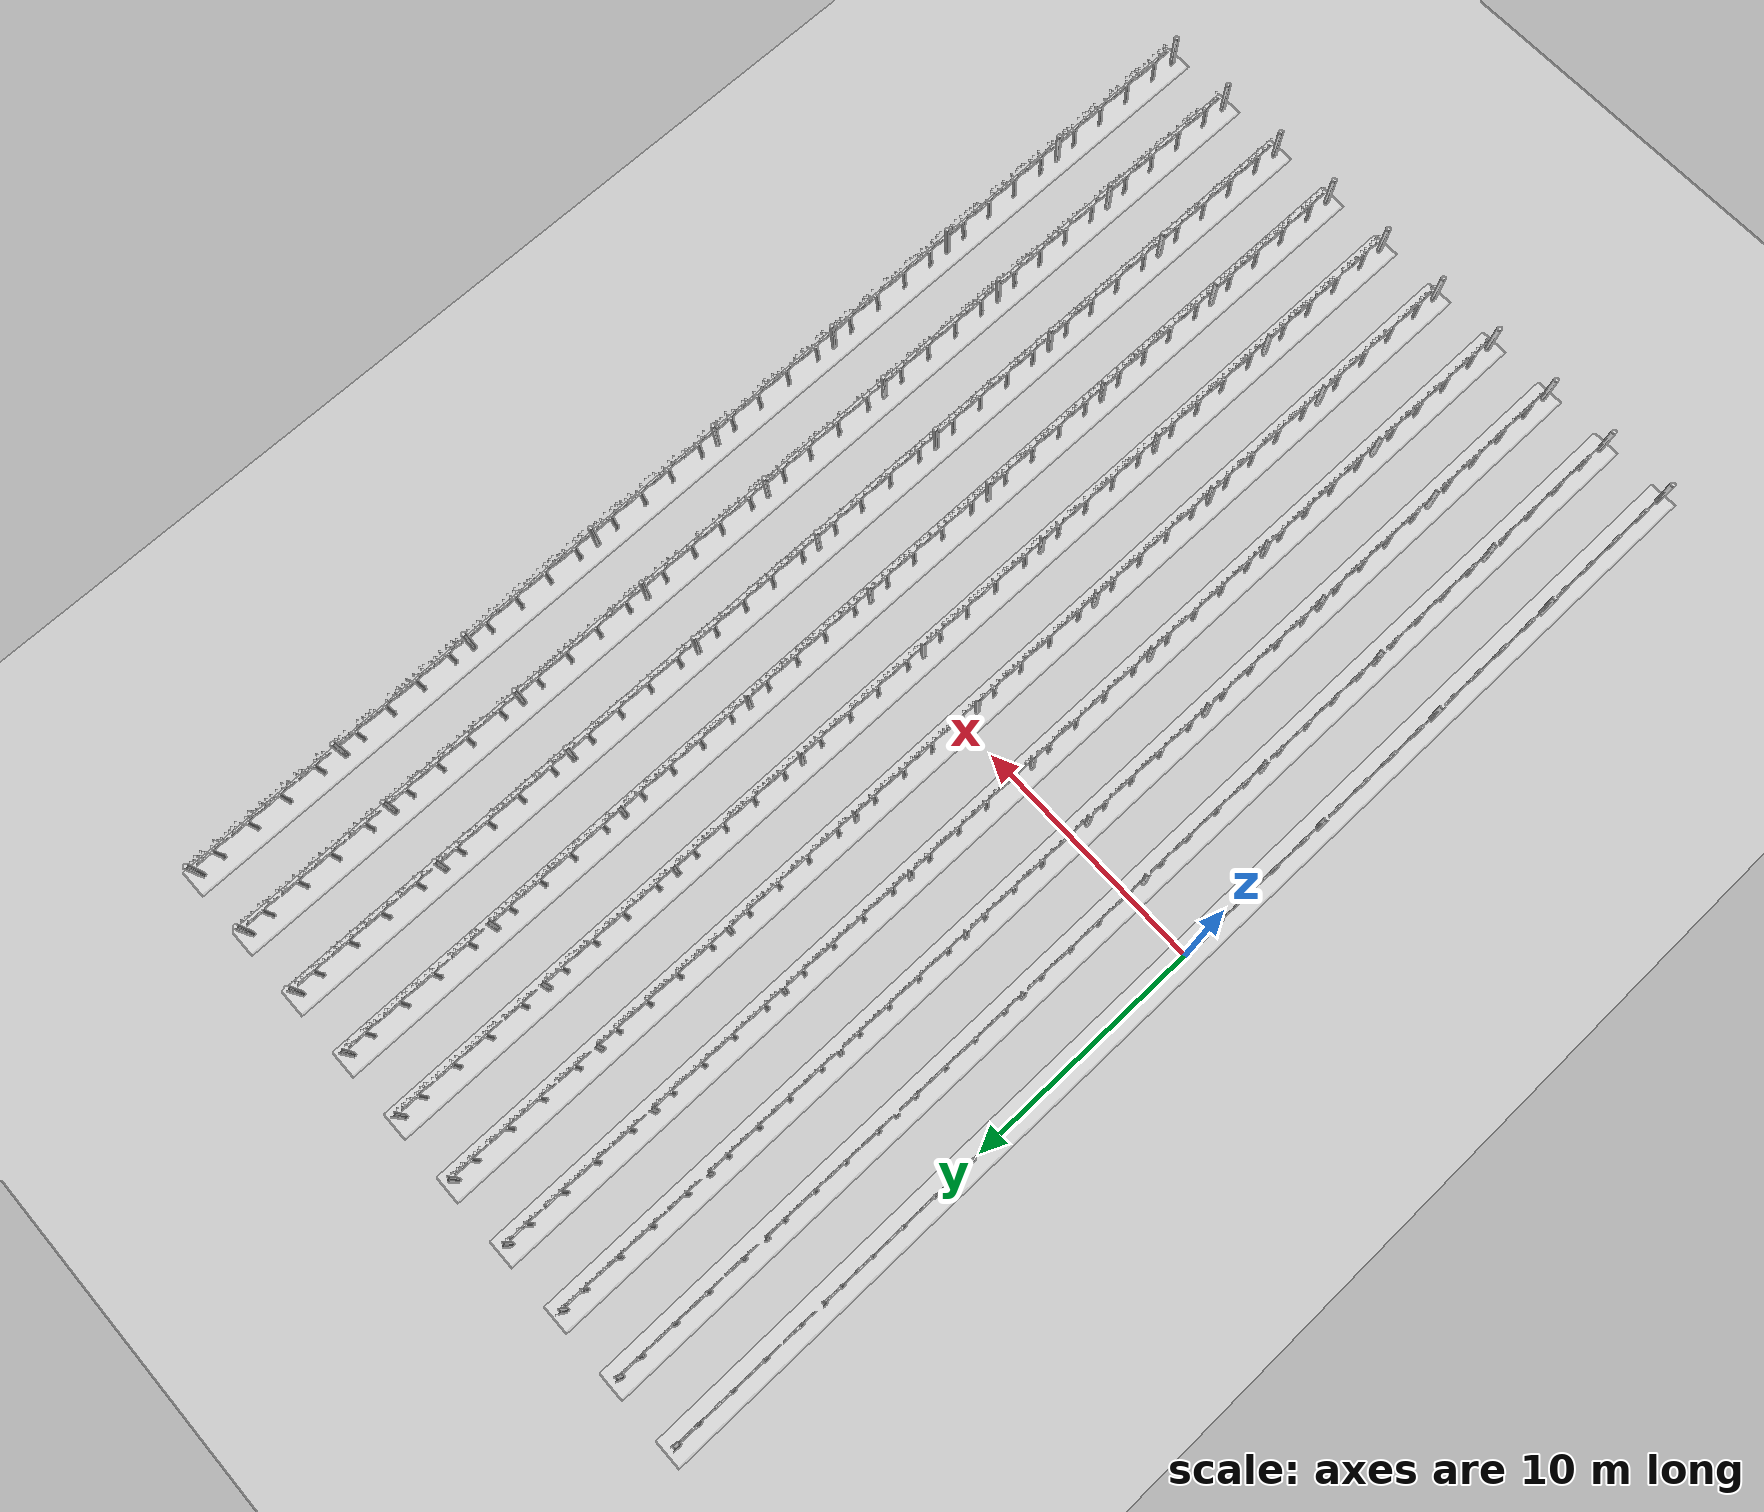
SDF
<sdf version="1.7">
 <world name="agropolis">
  <light name="sun" type="directional">
   <pose>0 0 10 0 -0 0</pose>
   <diffuse>0.8 0.8 0.8 1</diffuse>
   <specular>0.2 0.03 0.2 1</specular>
   <attenuation>
    <range>1000</range>
    <constant>0.9</constant>
    <linear>0.01</linear>
    <quadratic>0.001</quadratic>
   </attenuation>
   <direction>-0.5 0.1 -0.9</direction>
   <spot><inner_angle>0</inner_angle><outer_angle>0</outer_angle><falloff>0</falloff></spot>
  </light>
  <model name="ground_plane">
   <static>1</static>
   <link name="link">
    <collision name="collision">
     <geometry><plane><normal>0 0 1</normal><size>100 100</size></plane></geometry>
     <surface><friction><ode><mu>100</mu><mu2>50</mu2></ode></friction></surface>
    </collision>
    <visual name="visual">
     <cast_shadows>0</cast_shadows>
     <geometry><plane><normal>0 0 1</normal><size>100 100</size></plane></geometry>
     <material>
      <script><uri>file://media/materials/scripts/gazebo.material</uri><name>Gazebo/Grey</name></script>
     </material>
    </visual>
   </link>
  </model>
  <gravity>0 0 -9.8</gravity>
  <magnetic_field>6e-06 2.3e-05 -4.2e-05</magnetic_field>
  <atmosphere type="adiabatic"/>
  <physics type="ode">
   <max_step_size>0.001</max_step_size>
   <real_time_factor>1</real_time_factor>
   <real_time_update_rate>1000</real_time_update_rate>
  </physics>
  <scene><ambient>0.4 0.4 0.4 1</ambient><background>0.7 0.7 0.7 1</background><shadows>1</shadows></scene>
  <audio><device>default</device></audio>
  <spherical_coordinates>
   <surface_model>EARTH_WGS84</surface_model>
   <latitude_deg>41.288011</latitude_deg>
   <longitude_deg>2.045465</longitude_deg>
   <elevation>0</elevation>
   <heading_deg>0</heading_deg>
  </spherical_coordinates>
  <model name="fila1">
   <static>1</static>
   <link name="link">
    <collision name="collision">
     <geometry><mesh><uri>file://models/pasillo/meshes/pasillo.dae</uri></mesh></geometry>
    </collision>
    <visual name="visual">
     <geometry><mesh><uri>file://models/pasillo/meshes/pasillo.dae</uri></mesh></geometry>
    </visual>
   </link>
   <pose>0.0 -0.72112 0 0 -0 0</pose>
  </model>
  <model name="vinya_1_fila_1">
   <static>1</static>
   <link name="link">
    <collision name="collision">
     <geometry><mesh><uri>file://models/vinya/meshes/vinya.dae</uri></mesh></geometry>
    </collision>
    <visual name="visual">
     <geometry><mesh><uri>file://models/vinya/meshes/vinya.dae</uri></mesh></geometry>
    </visual>
   </link>
   <pose>0.0 -5.9 0.03 0 -0 1.57</pose>
  </model>
  <model name="vinya_2_fila_1">
   <static>1</static>
   <link name="link">
    <collision name="collision">
     <geometry><mesh><uri>file://models/vinya/meshes/vinya.dae</uri></mesh></geometry>
    </collision>
    <visual name="visual">
     <geometry><mesh><uri>file://models/vinya/meshes/vinya.dae</uri></mesh></geometry>
    </visual>
   </link>
   <pose>0.0 -4.40133 0.03 0 -0 1.57</pose>
  </model>
  <model name="vinya_3_fila_1">
   <static>1</static>
   <link name="link">
    <collision name="collision">
     <geometry><mesh><uri>file://models/vinya/meshes/vinya.dae</uri></mesh></geometry>
    </collision>
    <visual name="visual">
     <geometry><mesh><uri>file://models/vinya/meshes/vinya.dae</uri></mesh></geometry>
    </visual>
   </link>
   <pose>0.0 -2.94517 0.03 0 -0 1.57</pose>
  </model>
  <model name="vinya_4_fila_1">
   <static>1</static>
   <link name="link">
    <collision name="collision">
     <geometry><mesh><uri>file://models/vinya/meshes/vinya.dae</uri></mesh></geometry>
    </collision>
    <visual name="visual">
     <geometry><mesh><uri>file://models/vinya/meshes/vinya.dae</uri></mesh></geometry>
    </visual>
   </link>
   <pose>0.0 -1.60177 0.03 0 -0 1.57</pose>
  </model>
  <model name="vinya_5_fila_1">
   <static>1</static>
   <link name="link">
    <collision name="collision">
     <geometry><mesh><uri>file://models/vinya/meshes/vinya.dae</uri></mesh></geometry>
    </collision>
    <visual name="visual">
     <geometry><mesh><uri>file://models/vinya/meshes/vinya.dae</uri></mesh></geometry>
    </visual>
   </link>
   <pose>0.0 -7.64563 0.03 0 -0 1.57</pose>
  </model>
  <model name="vinya_6_fila_1">
   <static>1</static>
   <link name="link">
    <collision name="collision">
     <geometry><mesh><uri>file://models/vinya/meshes/vinya.dae</uri></mesh></geometry>
    </collision>
    <visual name="visual">
     <geometry><mesh><uri>file://models/vinya/meshes/vinya.dae</uri></mesh></geometry>
    </visual>
   </link>
   <pose>0.0 -9.06325 0.03 0 -0 1.57</pose>
  </model>
  <model name="vinya_7_fila_1">
   <static>1</static>
   <link name="link">
    <collision name="collision">
     <geometry><mesh><uri>file://models/vinya/meshes/vinya.dae</uri></mesh></geometry>
    </collision>
    <visual name="visual">
     <geometry><mesh><uri>file://models/vinya/meshes/vinya.dae</uri></mesh></geometry>
    </visual>
   </link>
   <pose>0.0 -10.4717 0.03 0 -0 1.57</pose>
  </model>
  <model name="vinya_8_fila_1">
   <static>1</static>
   <link name="link">
    <collision name="collision">
     <geometry><mesh><uri>file://models/vinya/meshes/vinya.dae</uri></mesh></geometry>
    </collision>
    <visual name="visual">
     <geometry><mesh><uri>file://models/vinya/meshes/vinya.dae</uri></mesh></geometry>
    </visual>
   </link>
   <pose>0.0 -11.8519 0.03 0 -0 1.57</pose>
  </model>
  <model name="vinya_9_fila_1">
   <static>1</static>
   <link name="link">
    <collision name="collision">
     <geometry><mesh><uri>file://models/vinya/meshes/vinya.dae</uri></mesh></geometry>
    </collision>
    <visual name="visual">
     <geometry><mesh><uri>file://models/vinya/meshes/vinya.dae</uri></mesh></geometry>
    </visual>
   </link>
   <pose>0.0 -13.6368 0.03 0 -0 1.57</pose>
  </model>
  <model name="vinya_10_fila_1">
   <static>1</static>
   <link name="link">
    <collision name="collision">
     <geometry><mesh><uri>file://models/vinya/meshes/vinya.dae</uri></mesh></geometry>
    </collision>
    <visual name="visual">
     <geometry><mesh><uri>file://models/vinya/meshes/vinya.dae</uri></mesh></geometry>
    </visual>
   </link>
   <pose>0.0 -14.9995 0.03 0 -0 1.57</pose>
  </model>
  <model name="vinya_11_fila_1">
   <static>1</static>
   <link name="link">
    <collision name="collision">
     <geometry><mesh><uri>file://models/vinya/meshes/vinya.dae</uri></mesh></geometry>
    </collision>
    <visual name="visual">
     <geometry><mesh><uri>file://models/vinya/meshes/vinya.dae</uri></mesh></geometry>
    </visual>
   </link>
   <pose>0.0 -16.381 0.03 0 -0 1.57</pose>
  </model>
  <model name="vinya_12_fila_1">
   <static>1</static>
   <link name="link">
    <collision name="collision">
     <geometry><mesh><uri>file://models/vinya/meshes/vinya.dae</uri></mesh></geometry>
    </collision>
    <visual name="visual">
     <geometry><mesh><uri>file://models/vinya/meshes/vinya.dae</uri></mesh></geometry>
    </visual>
   </link>
   <pose>0.0 -17.8271 0.03 0 -0 1.57</pose>
  </model>
  <model name="vinya_13_fila_1">
   <static>1</static>
   <link name="link">
    <collision name="collision">
     <geometry><mesh><uri>file://models/vinya/meshes/vinya.dae</uri></mesh></geometry>
    </collision>
    <visual name="visual">
     <geometry><mesh><uri>file://models/vinya/meshes/vinya.dae</uri></mesh></geometry>
    </visual>
   </link>
   <pose>0.0 -19.6679 0.03 0 -0 1.57</pose>
  </model>
  <model name="vinya_14_fila_1">
   <static>1</static>
   <link name="link">
    <collision name="collision">
     <geometry><mesh><uri>file://models/vinya/meshes/vinya.dae</uri></mesh></geometry>
    </collision>
    <visual name="visual">
     <geometry><mesh><uri>file://models/vinya/meshes/vinya.dae</uri></mesh></geometry>
    </visual>
   </link>
   <pose>0.0 -21.121 0.03 0 -0 1.57</pose>
  </model>
  <model name="vinya_15_fila_1">
   <static>1</static>
   <link name="link">
    <collision name="collision">
     <geometry><mesh><uri>file://models/vinya/meshes/vinya.dae</uri></mesh></geometry>
    </collision>
    <visual name="visual">
     <geometry><mesh><uri>file://models/vinya/meshes/vinya.dae</uri></mesh></geometry>
    </visual>
   </link>
   <pose>0.0 -22.6011 0.03 0 -0 1.57</pose>
  </model>
  <model name="vinya_16_fila_1">
   <static>1</static>
   <link name="link">
    <collision name="collision">
     <geometry><mesh><uri>file://models/vinya/meshes/vinya.dae</uri></mesh></geometry>
    </collision>
    <visual name="visual">
     <geometry><mesh><uri>file://models/vinya/meshes/vinya.dae</uri></mesh></geometry>
    </visual>
   </link>
   <pose>0.0 -24.1275 0.03 0 -0 1.57</pose>
  </model>
  <model name="vinya_17_fila_1">
   <static>1</static>
   <link name="link">
    <collision name="collision">
     <geometry><mesh><uri>file://models/vinya/meshes/vinya.dae</uri></mesh></geometry>
    </collision>
    <visual name="visual">
     <geometry><mesh><uri>file://models/vinya/meshes/vinya.dae</uri></mesh></geometry>
    </visual>
   </link>
   <pose>0.0 0.038395 0.03 0 -0 1.57</pose>
  </model>
  <model name="vinya_18_fila_1">
   <static>1</static>
   <link name="link">
    <collision name="collision">
     <geometry><mesh><uri>file://models/vinya/meshes/vinya.dae</uri></mesh></geometry>
    </collision>
    <visual name="visual">
     <geometry><mesh><uri>file://models/vinya/meshes/vinya.dae</uri></mesh></geometry>
    </visual>
   </link>
   <pose>0.0 1.51569 0.03 0 -0 1.57</pose>
  </model>
  <model name="vinya_19_fila_1">
   <static>1</static>
   <link name="link">
    <collision name="collision">
     <geometry><mesh><uri>file://models/vinya/meshes/vinya.dae</uri></mesh></geometry>
    </collision>
    <visual name="visual">
     <geometry><mesh><uri>file://models/vinya/meshes/vinya.dae</uri></mesh></geometry>
    </visual>
   </link>
   <pose>0.0 2.8899 0.03 0 -0 1.57</pose>
  </model>
  <model name="vinya_20_fila_1">
   <static>1</static>
   <link name="link">
    <collision name="collision">
     <geometry><mesh><uri>file://models/vinya/meshes/vinya.dae</uri></mesh></geometry>
    </collision>
    <visual name="visual">
     <geometry><mesh><uri>file://models/vinya/meshes/vinya.dae</uri></mesh></geometry>
    </visual>
   </link>
   <pose>0.0 4.31805 0.03 0 -0 1.57</pose>
  </model>
  <model name="vinya_21_fila_1">
   <static>1</static>
   <link name="link">
    <collision name="collision">
     <geometry><mesh><uri>file://models/vinya/meshes/vinya.dae</uri></mesh></geometry>
    </collision>
    <visual name="visual">
     <geometry><mesh><uri>file://models/vinya/meshes/vinya.dae</uri></mesh></geometry>
    </visual>
   </link>
   <pose>0.0 6.09459 0.03 0 -0 1.57</pose>
  </model>
  <model name="vinya_22_fila_1">
   <static>1</static>
   <link name="link">
    <collision name="collision">
     <geometry><mesh><uri>file://models/vinya/meshes/vinya.dae</uri></mesh></geometry>
    </collision>
    <visual name="visual">
     <geometry><mesh><uri>file://models/vinya/meshes/vinya.dae</uri></mesh></geometry>
    </visual>
   </link>
   <pose>0.0 7.52059 0.03 0 -0 1.57</pose>
  </model>
  <model name="vinya_23_fila_1">
   <static>1</static>
   <link name="link">
    <collision name="collision">
     <geometry><mesh><uri>file://models/vinya/meshes/vinya.dae</uri></mesh></geometry>
    </collision>
    <visual name="visual">
     <geometry><mesh><uri>file://models/vinya/meshes/vinya.dae</uri></mesh></geometry>
    </visual>
   </link>
   <pose>0.0 8.93263 0.03 0 -0 1.57</pose>
  </model>
  <model name="vinya_24_fila_1">
   <static>1</static>
   <link name="link">
    <collision name="collision">
     <geometry><mesh><uri>file://models/vinya/meshes/vinya.dae</uri></mesh></geometry>
    </collision>
    <visual name="visual">
     <geometry><mesh><uri>file://models/vinya/meshes/vinya.dae</uri></mesh></geometry>
    </visual>
   </link>
   <pose>0.0 10.3418 0.03 0 -0 1.57</pose>
  </model>
  <model name="vinya_25_fila_1">
   <static>1</static>
   <link name="link">
    <collision name="collision">
     <geometry><mesh><uri>file://models/vinya/meshes/vinya.dae</uri></mesh></geometry>
    </collision>
    <visual name="visual">
     <geometry><mesh><uri>file://models/vinya/meshes/vinya.dae</uri></mesh></geometry>
    </visual>
   </link>
   <pose>0.0 12.1 0.03 0 -0 1.57</pose>
  </model>
  <model name="vinya_26_fila_1">
   <static>1</static>
   <link name="link">
    <collision name="collision">
     <geometry><mesh><uri>file://models/vinya/meshes/vinya.dae</uri></mesh></geometry>
    </collision>
    <visual name="visual">
     <geometry><mesh><uri>file://models/vinya/meshes/vinya.dae</uri></mesh></geometry>
    </visual>
   </link>
   <pose>0.0 13.6 0.03 0 -0 1.57</pose>
  </model>
  <model name="vinya_27_fila_1">
   <static>1</static>
   <link name="link">
    <collision name="collision">
     <geometry><mesh><uri>file://models/vinya/meshes/vinya.dae</uri></mesh></geometry>
    </collision>
    <visual name="visual">
     <geometry><mesh><uri>file://models/vinya/meshes/vinya.dae</uri></mesh></geometry>
    </visual>
   </link>
   <pose>0.0 15 0.03 0 -0 1.57</pose>
  </model>
  <model name="vinya_28_fila_1">
   <static>1</static>
   <link name="link">
    <collision name="collision">
     <geometry><mesh><uri>file://models/vinya/meshes/vinya.dae</uri></mesh></geometry>
    </collision>
    <visual name="visual">
     <geometry><mesh><uri>file://models/vinya/meshes/vinya.dae</uri></mesh></geometry>
    </visual>
   </link>
   <pose>0.0 16.404 0.03 0 -0 1.57</pose>
  </model>
  <model name="vinya_29_fila_1">
   <static>1</static>
   <link name="link">
    <collision name="collision">
     <geometry><mesh><uri>file://models/vinya/meshes/vinya.dae</uri></mesh></geometry>
    </collision>
    <visual name="visual">
     <geometry><mesh><uri>file://models/vinya/meshes/vinya.dae</uri></mesh></geometry>
    </visual>
   </link>
   <pose>0.0 18.2453 0.03 0 -0 1.57</pose>
  </model>
  <model name="vinya_30_fila_1">
   <static>1</static>
   <link name="link">
    <collision name="collision">
     <geometry><mesh><uri>file://models/vinya/meshes/vinya.dae</uri></mesh></geometry>
    </collision>
    <visual name="visual">
     <geometry><mesh><uri>file://models/vinya/meshes/vinya.dae</uri></mesh></geometry>
    </visual>
   </link>
   <pose>0.0 19.8052 0.03 0 -0 1.57</pose>
  </model>
  <model name="vinya_31_fila_1">
   <static>1</static>
   <link name="link">
    <collision name="collision">
     <geometry><mesh><uri>file://models/vinya/meshes/vinya.dae</uri></mesh></geometry>
    </collision>
    <visual name="visual">
     <geometry><mesh><uri>file://models/vinya/meshes/vinya.dae</uri></mesh></geometry>
    </visual>
   </link>
   <pose>0.0 21.2672 0.03 0 -0 1.57</pose>
  </model>
  <model name="vinya_32_fila_1">
   <static>1</static>
   <link name="link">
    <collision name="collision">
     <geometry><mesh><uri>file://models/vinya/meshes/vinya.dae</uri></mesh></geometry>
    </collision>
    <visual name="visual">
     <geometry><mesh><uri>file://models/vinya/meshes/vinya.dae</uri></mesh></geometry>
    </visual>
   </link>
   <pose>0.0 22.8 0.03 0 -0 1.57</pose>
  </model>
  <model name="fila2">
   <static>1</static>
   <link name="link">
    <collision name="collision">
     <geometry><mesh><uri>file://models/pasillo/meshes/pasillo.dae</uri></mesh></geometry>
    </collision>
    <visual name="visual">
     <geometry><mesh><uri>file://models/pasillo/meshes/pasillo.dae</uri></mesh></geometry>
    </visual>
   </link>
   <pose>2.9 -0.72112 0 0 -0 0</pose>
  </model>
  <model name="vinya_1_fila_2">
   <static>1</static>
   <link name="link">
    <collision name="collision">
     <geometry><mesh><uri>file://models/vinya/meshes/vinya.dae</uri></mesh></geometry>
    </collision>
    <visual name="visual">
     <geometry><mesh><uri>file://models/vinya/meshes/vinya.dae</uri></mesh></geometry>
    </visual>
   </link>
   <pose>2.9 -5.9 0.03 0 -0 1.57</pose>
  </model>
  <model name="vinya_2_fila_2">
   <static>1</static>
   <link name="link">
    <collision name="collision">
     <geometry><mesh><uri>file://models/vinya/meshes/vinya.dae</uri></mesh></geometry>
    </collision>
    <visual name="visual">
     <geometry><mesh><uri>file://models/vinya/meshes/vinya.dae</uri></mesh></geometry>
    </visual>
   </link>
   <pose>2.9 -4.40133 0.03 0 -0 1.57</pose>
  </model>
  <model name="vinya_3_fila_2">
   <static>1</static>
   <link name="link">
    <collision name="collision">
     <geometry><mesh><uri>file://models/vinya/meshes/vinya.dae</uri></mesh></geometry>
    </collision>
    <visual name="visual">
     <geometry><mesh><uri>file://models/vinya/meshes/vinya.dae</uri></mesh></geometry>
    </visual>
   </link>
   <pose>2.9 -2.94517 0.03 0 -0 1.57</pose>
  </model>
  <model name="vinya_4_fila_2">
   <static>1</static>
   <link name="link">
    <collision name="collision">
     <geometry><mesh><uri>file://models/vinya/meshes/vinya.dae</uri></mesh></geometry>
    </collision>
    <visual name="visual">
     <geometry><mesh><uri>file://models/vinya/meshes/vinya.dae</uri></mesh></geometry>
    </visual>
   </link>
   <pose>2.9 -1.60177 0.03 0 -0 1.57</pose>
  </model>
  <model name="vinya_5_fila_2">
   <static>1</static>
   <link name="link">
    <collision name="collision">
     <geometry><mesh><uri>file://models/vinya/meshes/vinya.dae</uri></mesh></geometry>
    </collision>
    <visual name="visual">
     <geometry><mesh><uri>file://models/vinya/meshes/vinya.dae</uri></mesh></geometry>
    </visual>
   </link>
   <pose>2.9 -7.64563 0.03 0 -0 1.57</pose>
  </model>
  <model name="vinya_6_fila_2">
   <static>1</static>
   <link name="link">
    <collision name="collision">
     <geometry><mesh><uri>file://models/vinya/meshes/vinya.dae</uri></mesh></geometry>
    </collision>
    <visual name="visual">
     <geometry><mesh><uri>file://models/vinya/meshes/vinya.dae</uri></mesh></geometry>
    </visual>
   </link>
   <pose>2.9 -9.06325 0.03 0 -0 1.57</pose>
  </model>
  <model name="vinya_7_fila_2">
   <static>1</static>
   <link name="link">
    <collision name="collision">
     <geometry><mesh><uri>file://models/vinya/meshes/vinya.dae</uri></mesh></geometry>
    </collision>
    <visual name="visual">
     <geometry><mesh><uri>file://models/vinya/meshes/vinya.dae</uri></mesh></geometry>
    </visual>
   </link>
   <pose>2.9 -10.4717 0.03 0 -0 1.57</pose>
  </model>
  <model name="vinya_8_fila_2">
   <static>1</static>
   <link name="link">
    <collision name="collision">
     <geometry><mesh><uri>file://models/vinya/meshes/vinya.dae</uri></mesh></geometry>
    </collision>
    <visual name="visual">
     <geometry><mesh><uri>file://models/vinya/meshes/vinya.dae</uri></mesh></geometry>
    </visual>
   </link>
   <pose>2.9 -11.8519 0.03 0 -0 1.57</pose>
  </model>
  <model name="vinya_9_fila_2">
   <static>1</static>
   <link name="link">
    <collision name="collision">
     <geometry><mesh><uri>file://models/vinya/meshes/vinya.dae</uri></mesh></geometry>
    </collision>
    <visual name="visual">
     <geometry><mesh><uri>file://models/vinya/meshes/vinya.dae</uri></mesh></geometry>
    </visual>
   </link>
   <pose>2.9 -13.6368 0.03 0 -0 1.57</pose>
  </model>
  <model name="vinya_10_fila_2">
   <static>1</static>
   <link name="link">
    <collision name="collision">
     <geometry><mesh><uri>file://models/vinya/meshes/vinya.dae</uri></mesh></geometry>
    </collision>
    <visual name="visual">
     <geometry><mesh><uri>file://models/vinya/meshes/vinya.dae</uri></mesh></geometry>
    </visual>
   </link>
   <pose>2.9 -14.9995 0.03 0 -0 1.57</pose>
  </model>
  <model name="vinya_11_fila_2">
   <static>1</static>
   <link name="link">
    <collision name="collision">
     <geometry><mesh><uri>file://models/vinya/meshes/vinya.dae</uri></mesh></geometry>
    </collision>
    <visual name="visual">
     <geometry><mesh><uri>file://models/vinya/meshes/vinya.dae</uri></mesh></geometry>
    </visual>
   </link>
   <pose>2.9 -16.381 0.03 0 -0 1.57</pose>
  </model>
  <model name="vinya_12_fila_2">
   <static>1</static>
   <link name="link">
    <collision name="collision">
     <geometry><mesh><uri>file://models/vinya/meshes/vinya.dae</uri></mesh></geometry>
    </collision>
    <visual name="visual">
     <geometry><mesh><uri>file://models/vinya/meshes/vinya.dae</uri></mesh></geometry>
    </visual>
   </link>
   <pose>2.9 -17.8271 0.03 0 -0 1.57</pose>
  </model>
  <model name="vinya_13_fila_2">
   <static>1</static>
   <link name="link">
    <collision name="collision">
     <geometry><mesh><uri>file://models/vinya/meshes/vinya.dae</uri></mesh></geometry>
    </collision>
    <visual name="visual">
     <geometry><mesh><uri>file://models/vinya/meshes/vinya.dae</uri></mesh></geometry>
    </visual>
   </link>
   <pose>2.9 -19.6679 0.03 0 -0 1.57</pose>
  </model>
  <model name="vinya_14_fila_2">
   <static>1</static>
   <link name="link">
    <collision name="collision">
     <geometry><mesh><uri>file://models/vinya/meshes/vinya.dae</uri></mesh></geometry>
    </collision>
    <visual name="visual">
     <geometry><mesh><uri>file://models/vinya/meshes/vinya.dae</uri></mesh></geometry>
    </visual>
   </link>
   <pose>2.9 -21.121 0.03 0 -0 1.57</pose>
  </model>
  <model name="vinya_15_fila_2">
   <static>1</static>
   <link name="link">
    <collision name="collision">
     <geometry><mesh><uri>file://models/vinya/meshes/vinya.dae</uri></mesh></geometry>
    </collision>
    <visual name="visual">
     <geometry><mesh><uri>file://models/vinya/meshes/vinya.dae</uri></mesh></geometry>
    </visual>
   </link>
   <pose>2.9 -22.6011 0.03 0 -0 1.57</pose>
  </model>
  <model name="vinya_16_fila_2">
   <static>1</static>
   <link name="link">
    <collision name="collision">
     <geometry><mesh><uri>file://models/vinya/meshes/vinya.dae</uri></mesh></geometry>
    </collision>
    <visual name="visual">
     <geometry><mesh><uri>file://models/vinya/meshes/vinya.dae</uri></mesh></geometry>
    </visual>
   </link>
   <pose>2.9 -24.1275 0.03 0 -0 1.57</pose>
  </model>
  <model name="vinya_17_fila_2">
   <static>1</static>
   <link name="link">
    <collision name="collision">
     <geometry><mesh><uri>file://models/vinya/meshes/vinya.dae</uri></mesh></geometry>
    </collision>
    <visual name="visual">
     <geometry><mesh><uri>file://models/vinya/meshes/vinya.dae</uri></mesh></geometry>
    </visual>
   </link>
   <pose>2.9 0.038395 0.03 0 -0 1.57</pose>
  </model>
  <model name="vinya_18_fila_2">
   <static>1</static>
   <link name="link">
    <collision name="collision">
     <geometry><mesh><uri>file://models/vinya/meshes/vinya.dae</uri></mesh></geometry>
    </collision>
    <visual name="visual">
     <geometry><mesh><uri>file://models/vinya/meshes/vinya.dae</uri></mesh></geometry>
    </visual>
   </link>
   <pose>2.9 1.51569 0.03 0 -0 1.57</pose>
  </model>
  <model name="vinya_19_fila_2">
   <static>1</static>
   <link name="link">
    <collision name="collision">
     <geometry><mesh><uri>file://models/vinya/meshes/vinya.dae</uri></mesh></geometry>
    </collision>
    <visual name="visual">
     <geometry><mesh><uri>file://models/vinya/meshes/vinya.dae</uri></mesh></geometry>
    </visual>
   </link>
   <pose>2.9 2.8899 0.03 0 -0 1.57</pose>
  </model>
  <model name="vinya_20_fila_2">
   <static>1</static>
   <link name="link">
    <collision name="collision">
     <geometry><mesh><uri>file://models/vinya/meshes/vinya.dae</uri></mesh></geometry>
    </collision>
    <visual name="visual">
     <geometry><mesh><uri>file://models/vinya/meshes/vinya.dae</uri></mesh></geometry>
    </visual>
   </link>
   <pose>2.9 4.31805 0.03 0 -0 1.57</pose>
  </model>
  <model name="vinya_21_fila_2">
   <static>1</static>
   <link name="link">
    <collision name="collision">
     <geometry><mesh><uri>file://models/vinya/meshes/vinya.dae</uri></mesh></geometry>
    </collision>
    <visual name="visual">
     <geometry><mesh><uri>file://models/vinya/meshes/vinya.dae</uri></mesh></geometry>
    </visual>
   </link>
   <pose>2.9 6.09459 0.03 0 -0 1.57</pose>
  </model>
  <model name="vinya_22_fila_2">
   <static>1</static>
   <link name="link">
    <collision name="collision">
     <geometry><mesh><uri>file://models/vinya/meshes/vinya.dae</uri></mesh></geometry>
    </collision>
    <visual name="visual">
     <geometry><mesh><uri>file://models/vinya/meshes/vinya.dae</uri></mesh></geometry>
    </visual>
   </link>
   <pose>2.9 7.52059 0.03 0 -0 1.57</pose>
  </model>
  <model name="vinya_23_fila_2">
   <static>1</static>
   <link name="link">
    <collision name="collision">
     <geometry><mesh><uri>file://models/vinya/meshes/vinya.dae</uri></mesh></geometry>
    </collision>
    <visual name="visual">
     <geometry><mesh><uri>file://models/vinya/meshes/vinya.dae</uri></mesh></geometry>
    </visual>
   </link>
   <pose>2.9 8.93263 0.03 0 -0 1.57</pose>
  </model>
  <model name="vinya_24_fila_2">
   <static>1</static>
   <link name="link">
    <collision name="collision">
     <geometry><mesh><uri>file://models/vinya/meshes/vinya.dae</uri></mesh></geometry>
    </collision>
    <visual name="visual">
     <geometry><mesh><uri>file://models/vinya/meshes/vinya.dae</uri></mesh></geometry>
    </visual>
   </link>
   <pose>2.9 10.3418 0.03 0 -0 1.57</pose>
  </model>
  <model name="vinya_25_fila_2">
   <static>1</static>
   <link name="link">
    <collision name="collision">
     <geometry><mesh><uri>file://models/vinya/meshes/vinya.dae</uri></mesh></geometry>
    </collision>
    <visual name="visual">
     <geometry><mesh><uri>file://models/vinya/meshes/vinya.dae</uri></mesh></geometry>
    </visual>
   </link>
   <pose>2.9 12.1 0.03 0 -0 1.57</pose>
  </model>
  <model name="vinya_26_fila_2">
   <static>1</static>
   <link name="link">
    <collision name="collision">
     <geometry><mesh><uri>file://models/vinya/meshes/vinya.dae</uri></mesh></geometry>
    </collision>
    <visual name="visual">
     <geometry><mesh><uri>file://models/vinya/meshes/vinya.dae</uri></mesh></geometry>
    </visual>
   </link>
   <pose>2.9 13.6 0.03 0 -0 1.57</pose>
  </model>
  <model name="vinya_27_fila_2">
   <static>1</static>
   <link name="link">
    <collision name="collision">
     <geometry><mesh><uri>file://models/vinya/meshes/vinya.dae</uri></mesh></geometry>
    </collision>
    <visual name="visual">
     <geometry><mesh><uri>file://models/vinya/meshes/vinya.dae</uri></mesh></geometry>
    </visual>
   </link>
   <pose>2.9 15 0.03 0 -0 1.57</pose>
  </model>
  <model name="vinya_28_fila_2">
   <static>1</static>
   <link name="link">
    <collision name="collision">
     <geometry><mesh><uri>file://models/vinya/meshes/vinya.dae</uri></mesh></geometry>
    </collision>
    <visual name="visual">
     <geometry><mesh><uri>file://models/vinya/meshes/vinya.dae</uri></mesh></geometry>
    </visual>
   </link>
   <pose>2.9 16.404 0.03 0 -0 1.57</pose>
  </model>
  <model name="vinya_29_fila_2">
   <static>1</static>
   <link name="link">
    <collision name="collision">
     <geometry><mesh><uri>file://models/vinya/meshes/vinya.dae</uri></mesh></geometry>
    </collision>
    <visual name="visual">
     <geometry><mesh><uri>file://models/vinya/meshes/vinya.dae</uri></mesh></geometry>
    </visual>
   </link>
   <pose>2.9 18.2453 0.03 0 -0 1.57</pose>
  </model>
  <model name="vinya_30_fila_2">
   <static>1</static>
   <link name="link">
    <collision name="collision">
     <geometry><mesh><uri>file://models/vinya/meshes/vinya.dae</uri></mesh></geometry>
    </collision>
    <visual name="visual">
     <geometry><mesh><uri>file://models/vinya/meshes/vinya.dae</uri></mesh></geometry>
    </visual>
   </link>
   <pose>2.9 19.8052 0.03 0 -0 1.57</pose>
  </model>
  <model name="vinya_31_fila_2">
   <static>1</static>
   <link name="link">
    <collision name="collision">
     <geometry><mesh><uri>file://models/vinya/meshes/vinya.dae</uri></mesh></geometry>
    </collision>
    <visual name="visual">
     <geometry><mesh><uri>file://models/vinya/meshes/vinya.dae</uri></mesh></geometry>
    </visual>
   </link>
   <pose>2.9 21.2672 0.03 0 -0 1.57</pose>
  </model>
  <model name="vinya_32_fila_2">
   <static>1</static>
   <link name="link">
    <collision name="collision">
     <geometry><mesh><uri>file://models/vinya/meshes/vinya.dae</uri></mesh></geometry>
    </collision>
    <visual name="visual">
     <geometry><mesh><uri>file://models/vinya/meshes/vinya.dae</uri></mesh></geometry>
    </visual>
   </link>
   <pose>2.9 22.8 0.03 0 -0 1.57</pose>
  </model>
  <model name="fila3">
   <static>1</static>
   <link name="link">
    <collision name="collision">
     <geometry><mesh><uri>file://models/pasillo/meshes/pasillo.dae</uri></mesh></geometry>
    </collision>
    <visual name="visual">
     <geometry><mesh><uri>file://models/pasillo/meshes/pasillo.dae</uri></mesh></geometry>
    </visual>
   </link>
   <pose>5.8 -0.72112 0 0 -0 0</pose>
  </model>
  <model name="vinya_1_fila_3">
   <static>1</static>
   <link name="link">
    <collision name="collision">
     <geometry><mesh><uri>file://models/vinya/meshes/vinya.dae</uri></mesh></geometry>
    </collision>
    <visual name="visual">
     <geometry><mesh><uri>file://models/vinya/meshes/vinya.dae</uri></mesh></geometry>
    </visual>
   </link>
   <pose>5.8 -5.9 0.03 0 -0 1.57</pose>
  </model>
  <model name="vinya_2_fila_3">
   <static>1</static>
   <link name="link">
    <collision name="collision">
     <geometry><mesh><uri>file://models/vinya/meshes/vinya.dae</uri></mesh></geometry>
    </collision>
    <visual name="visual">
     <geometry><mesh><uri>file://models/vinya/meshes/vinya.dae</uri></mesh></geometry>
    </visual>
   </link>
   <pose>5.8 -4.40133 0.03 0 -0 1.57</pose>
  </model>
  <model name="vinya_3_fila_3">
   <static>1</static>
   <link name="link">
    <collision name="collision">
     <geometry><mesh><uri>file://models/vinya/meshes/vinya.dae</uri></mesh></geometry>
    </collision>
    <visual name="visual">
     <geometry><mesh><uri>file://models/vinya/meshes/vinya.dae</uri></mesh></geometry>
    </visual>
   </link>
   <pose>5.8 -2.94517 0.03 0 -0 1.57</pose>
  </model>
  <model name="vinya_4_fila_3">
   <static>1</static>
   <link name="link">
    <collision name="collision">
     <geometry><mesh><uri>file://models/vinya/meshes/vinya.dae</uri></mesh></geometry>
    </collision>
    <visual name="visual">
     <geometry><mesh><uri>file://models/vinya/meshes/vinya.dae</uri></mesh></geometry>
    </visual>
   </link>
   <pose>5.8 -1.60177 0.03 0 -0 1.57</pose>
  </model>
  <model name="vinya_5_fila_3">
   <static>1</static>
   <link name="link">
    <collision name="collision">
     <geometry><mesh><uri>file://models/vinya/meshes/vinya.dae</uri></mesh></geometry>
    </collision>
    <visual name="visual">
     <geometry><mesh><uri>file://models/vinya/meshes/vinya.dae</uri></mesh></geometry>
    </visual>
   </link>
   <pose>5.8 -7.64563 0.03 0 -0 1.57</pose>
  </model>
  <model name="vinya_6_fila_3">
   <static>1</static>
   <link name="link">
    <collision name="collision">
     <geometry><mesh><uri>file://models/vinya/meshes/vinya.dae</uri></mesh></geometry>
    </collision>
    <visual name="visual">
     <geometry><mesh><uri>file://models/vinya/meshes/vinya.dae</uri></mesh></geometry>
    </visual>
   </link>
   <pose>5.8 -9.06325 0.03 0 -0 1.57</pose>
  </model>
  <model name="vinya_7_fila_3">
   <static>1</static>
   <link name="link">
    <collision name="collision">
     <geometry><mesh><uri>file://models/vinya/meshes/vinya.dae</uri></mesh></geometry>
    </collision>
    <visual name="visual">
     <geometry><mesh><uri>file://models/vinya/meshes/vinya.dae</uri></mesh></geometry>
    </visual>
   </link>
   <pose>5.8 -10.4717 0.03 0 -0 1.57</pose>
  </model>
  <model name="vinya_8_fila_3">
   <static>1</static>
   <link name="link">
    <collision name="collision">
     <geometry><mesh><uri>file://models/vinya/meshes/vinya.dae</uri></mesh></geometry>
    </collision>
    <visual name="visual">
     <geometry><mesh><uri>file://models/vinya/meshes/vinya.dae</uri></mesh></geometry>
    </visual>
   </link>
   <pose>5.8 -11.8519 0.03 0 -0 1.57</pose>
  </model>
  <model name="vinya_9_fila_3">
   <static>1</static>
   <link name="link">
    <collision name="collision">
     <geometry><mesh><uri>file://models/vinya/meshes/vinya.dae</uri></mesh></geometry>
    </collision>
    <visual name="visual">
     <geometry><mesh><uri>file://models/vinya/meshes/vinya.dae</uri></mesh></geometry>
    </visual>
   </link>
   <pose>5.8 -13.6368 0.03 0 -0 1.57</pose>
  </model>
  <model name="vinya_10_fila_3">
   <static>1</static>
   <link name="link">
    <collision name="collision">
     <geometry><mesh><uri>file://models/vinya/meshes/vinya.dae</uri></mesh></geometry>
    </collision>
    <visual name="visual">
     <geometry><mesh><uri>file://models/vinya/meshes/vinya.dae</uri></mesh></geometry>
    </visual>
   </link>
   <pose>5.8 -14.9995 0.03 0 -0 1.57</pose>
  </model>
  <model name="vinya_11_fila_3">
   <static>1</static>
   <link name="link">
    <collision name="collision">
     <geometry><mesh><uri>file://models/vinya/meshes/vinya.dae</uri></mesh></geometry>
    </collision>
    <visual name="visual">
     <geometry><mesh><uri>file://models/vinya/meshes/vinya.dae</uri></mesh></geometry>
    </visual>
   </link>
   <pose>5.8 -16.381 0.03 0 -0 1.57</pose>
  </model>
  <model name="vinya_12_fila_3">
   <static>1</static>
   <link name="link">
    <collision name="collision">
     <geometry><mesh><uri>file://models/vinya/meshes/vinya.dae</uri></mesh></geometry>
    </collision>
    <visual name="visual">
     <geometry><mesh><uri>file://models/vinya/meshes/vinya.dae</uri></mesh></geometry>
    </visual>
   </link>
   <pose>5.8 -17.8271 0.03 0 -0 1.57</pose>
  </model>
  <model name="vinya_13_fila_3">
   <static>1</static>
   <link name="link">
    <collision name="collision">
     <geometry><mesh><uri>file://models/vinya/meshes/vinya.dae</uri></mesh></geometry>
    </collision>
    <visual name="visual">
     <geometry><mesh><uri>file://models/vinya/meshes/vinya.dae</uri></mesh></geometry>
    </visual>
   </link>
   <pose>5.8 -19.6679 0.03 0 -0 1.57</pose>
  </model>
  <model name="vinya_14_fila_3">
   <static>1</static>
   <link name="link">
    <collision name="collision">
     <geometry><mesh><uri>file://models/vinya/meshes/vinya.dae</uri></mesh></geometry>
    </collision>
    <visual name="visual">
     <geometry><mesh><uri>file://models/vinya/meshes/vinya.dae</uri></mesh></geometry>
    </visual>
   </link>
   <pose>5.8 -21.121 0.03 0 -0 1.57</pose>
  </model>
  <model name="vinya_15_fila_3">
   <static>1</static>
   <link name="link">
    <collision name="collision">
     <geometry><mesh><uri>file://models/vinya/meshes/vinya.dae</uri></mesh></geometry>
    </collision>
    <visual name="visual">
     <geometry><mesh><uri>file://models/vinya/meshes/vinya.dae</uri></mesh></geometry>
    </visual>
   </link>
   <pose>5.8 -22.6011 0.03 0 -0 1.57</pose>
  </model>
  <model name="vinya_16_fila_3">
   <static>1</static>
   <link name="link">
    <collision name="collision">
     <geometry><mesh><uri>file://models/vinya/meshes/vinya.dae</uri></mesh></geometry>
    </collision>
    <visual name="visual">
     <geometry><mesh><uri>file://models/vinya/meshes/vinya.dae</uri></mesh></geometry>
    </visual>
   </link>
   <pose>5.8 -24.1275 0.03 0 -0 1.57</pose>
  </model>
  <model name="vinya_17_fila_3">
   <static>1</static>
   <link name="link">
    <collision name="collision">
     <geometry><mesh><uri>file://models/vinya/meshes/vinya.dae</uri></mesh></geometry>
    </collision>
    <visual name="visual">
     <geometry><mesh><uri>file://models/vinya/meshes/vinya.dae</uri></mesh></geometry>
    </visual>
   </link>
   <pose>5.8 0.038395 0.03 0 -0 1.57</pose>
  </model>
  <model name="vinya_18_fila_3">
   <static>1</static>
   <link name="link">
    <collision name="collision">
     <geometry><mesh><uri>file://models/vinya/meshes/vinya.dae</uri></mesh></geometry>
    </collision>
    <visual name="visual">
     <geometry><mesh><uri>file://models/vinya/meshes/vinya.dae</uri></mesh></geometry>
    </visual>
   </link>
   <pose>5.8 1.51569 0.03 0 -0 1.57</pose>
  </model>
  <model name="vinya_19_fila_3">
   <static>1</static>
   <link name="link">
    <collision name="collision">
     <geometry><mesh><uri>file://models/vinya/meshes/vinya.dae</uri></mesh></geometry>
    </collision>
    <visual name="visual">
     <geometry><mesh><uri>file://models/vinya/meshes/vinya.dae</uri></mesh></geometry>
    </visual>
   </link>
   <pose>5.8 2.8899 0.03 0 -0 1.57</pose>
  </model>
  <model name="vinya_20_fila_3">
   <static>1</static>
   <link name="link">
    <collision name="collision">
     <geometry><mesh><uri>file://models/vinya/meshes/vinya.dae</uri></mesh></geometry>
    </collision>
    <visual name="visual">
     <geometry><mesh><uri>file://models/vinya/meshes/vinya.dae</uri></mesh></geometry>
    </visual>
   </link>
   <pose>5.8 4.31805 0.03 0 -0 1.57</pose>
  </model>
  <model name="vinya_21_fila_3">
   <static>1</static>
   <link name="link">
    <collision name="collision">
     <geometry><mesh><uri>file://models/vinya/meshes/vinya.dae</uri></mesh></geometry>
    </collision>
    <visual name="visual">
     <geometry><mesh><uri>file://models/vinya/meshes/vinya.dae</uri></mesh></geometry>
    </visual>
   </link>
   <pose>5.8 6.09459 0.03 0 -0 1.57</pose>
  </model>
  <model name="vinya_22_fila_3">
   <static>1</static>
   <link name="link">
    <collision name="collision">
     <geometry><mesh><uri>file://models/vinya/meshes/vinya.dae</uri></mesh></geometry>
    </collision>
    <visual name="visual">
     <geometry><mesh><uri>file://models/vinya/meshes/vinya.dae</uri></mesh></geometry>
    </visual>
   </link>
   <pose>5.8 7.52059 0.03 0 -0 1.57</pose>
  </model>
  <model name="vinya_23_fila_3">
   <static>1</static>
   <link name="link">
    <collision name="collision">
     <geometry><mesh><uri>file://models/vinya/meshes/vinya.dae</uri></mesh></geometry>
    </collision>
    <visual name="visual">
     <geometry><mesh><uri>file://models/vinya/meshes/vinya.dae</uri></mesh></geometry>
    </visual>
   </link>
   <pose>5.8 8.93263 0.03 0 -0 1.57</pose>
  </model>
  <model name="vinya_24_fila_3">
   <static>1</static>
   <link name="link">
    <collision name="collision">
     <geometry><mesh><uri>file://models/vinya/meshes/vinya.dae</uri></mesh></geometry>
    </collision>
    <visual name="visual">
     <geometry><mesh><uri>file://models/vinya/meshes/vinya.dae</uri></mesh></geometry>
    </visual>
   </link>
   <pose>5.8 10.3418 0.03 0 -0 1.57</pose>
  </model>
  <model name="vinya_25_fila_3">
   <static>1</static>
   <link name="link">
    <collision name="collision">
     <geometry><mesh><uri>file://models/vinya/meshes/vinya.dae</uri></mesh></geometry>
    </collision>
    <visual name="visual">
     <geometry><mesh><uri>file://models/vinya/meshes/vinya.dae</uri></mesh></geometry>
    </visual>
   </link>
   <pose>5.8 12.1 0.03 0 -0 1.57</pose>
  </model>
  <model name="vinya_26_fila_3">
   <static>1</static>
   <link name="link">
    <collision name="collision">
     <geometry><mesh><uri>file://models/vinya/meshes/vinya.dae</uri></mesh></geometry>
    </collision>
    <visual name="visual">
     <geometry><mesh><uri>file://models/vinya/meshes/vinya.dae</uri></mesh></geometry>
    </visual>
   </link>
   <pose>5.8 13.6 0.03 0 -0 1.57</pose>
  </model>
  <model name="vinya_27_fila_3">
   <static>1</static>
   <link name="link">
    <collision name="collision">
     <geometry><mesh><uri>file://models/vinya/meshes/vinya.dae</uri></mesh></geometry>
    </collision>
    <visual name="visual">
     <geometry><mesh><uri>file://models/vinya/meshes/vinya.dae</uri></mesh></geometry>
    </visual>
   </link>
   <pose>5.8 15 0.03 0 -0 1.57</pose>
  </model>
  <model name="vinya_28_fila_3">
   <static>1</static>
   <link name="link">
    <collision name="collision">
     <geometry><mesh><uri>file://models/vinya/meshes/vinya.dae</uri></mesh></geometry>
    </collision>
    <visual name="visual">
     <geometry><mesh><uri>file://models/vinya/meshes/vinya.dae</uri></mesh></geometry>
    </visual>
   </link>
   <pose>5.8 16.404 0.03 0 -0 1.57</pose>
  </model>
  <model name="vinya_29_fila_3">
   <static>1</static>
   <link name="link">
    <collision name="collision">
     <geometry><mesh><uri>file://models/vinya/meshes/vinya.dae</uri></mesh></geometry>
    </collision>
    <visual name="visual">
     <geometry><mesh><uri>file://models/vinya/meshes/vinya.dae</uri></mesh></geometry>
    </visual>
   </link>
   <pose>5.8 18.2453 0.03 0 -0 1.57</pose>
  </model>
  <model name="vinya_30_fila_3">
   <static>1</static>
   <link name="link">
    <collision name="collision">
     <geometry><mesh><uri>file://models/vinya/meshes/vinya.dae</uri></mesh></geometry>
    </collision>
    <visual name="visual">
     <geometry><mesh><uri>file://models/vinya/meshes/vinya.dae</uri></mesh></geometry>
    </visual>
   </link>
   <pose>5.8 19.8052 0.03 0 -0 1.57</pose>
  </model>
  <model name="vinya_31_fila_3">
   <static>1</static>
   <link name="link">
    <collision name="collision">
     <geometry><mesh><uri>file://models/vinya/meshes/vinya.dae</uri></mesh></geometry>
    </collision>
    <visual name="visual">
     <geometry><mesh><uri>file://models/vinya/meshes/vinya.dae</uri></mesh></geometry>
    </visual>
   </link>
   <pose>5.8 21.2672 0.03 0 -0 1.57</pose>
  </model>
  <model name="vinya_32_fila_3">
   <static>1</static>
   <link name="link">
    <collision name="collision">
     <geometry><mesh><uri>file://models/vinya/meshes/vinya.dae</uri></mesh></geometry>
    </collision>
    <visual name="visual">
     <geometry><mesh><uri>file://models/vinya/meshes/vinya.dae</uri></mesh></geometry>
    </visual>
   </link>
   <pose>5.8 22.8 0.03 0 -0 1.57</pose>
  </model>
  <model name="fila4">
   <static>1</static>
   <link name="link">
    <collision name="collision">
     <geometry><mesh><uri>file://models/pasillo/meshes/pasillo.dae</uri></mesh></geometry>
    </collision>
    <visual name="visual">
     <geometry><mesh><uri>file://models/pasillo/meshes/pasillo.dae</uri></mesh></geometry>
    </visual>
   </link>
   <pose>8.7 -0.72112 0 0 -0 0</pose>
  </model>
  <model name="vinya_1_fila_4">
   <static>1</static>
   <link name="link">
    <collision name="collision">
     <geometry><mesh><uri>file://models/vinya/meshes/vinya.dae</uri></mesh></geometry>
    </collision>
    <visual name="visual">
     <geometry><mesh><uri>file://models/vinya/meshes/vinya.dae</uri></mesh></geometry>
    </visual>
   </link>
   <pose>8.7 -5.9 0.03 0 -0 1.57</pose>
  </model>
  <model name="vinya_2_fila_4">
   <static>1</static>
   <link name="link">
    <collision name="collision">
     <geometry><mesh><uri>file://models/vinya/meshes/vinya.dae</uri></mesh></geometry>
    </collision>
    <visual name="visual">
     <geometry><mesh><uri>file://models/vinya/meshes/vinya.dae</uri></mesh></geometry>
    </visual>
   </link>
   <pose>8.7 -4.40133 0.03 0 -0 1.57</pose>
  </model>
  <model name="vinya_3_fila_4">
   <static>1</static>
   <link name="link">
    <collision name="collision">
     <geometry><mesh><uri>file://models/vinya/meshes/vinya.dae</uri></mesh></geometry>
    </collision>
    <visual name="visual">
     <geometry><mesh><uri>file://models/vinya/meshes/vinya.dae</uri></mesh></geometry>
    </visual>
   </link>
   <pose>8.7 -2.94517 0.03 0 -0 1.57</pose>
  </model>
  <model name="vinya_4_fila_4">
   <static>1</static>
   <link name="link">
    <collision name="collision">
     <geometry><mesh><uri>file://models/vinya/meshes/vinya.dae</uri></mesh></geometry>
    </collision>
    <visual name="visual">
     <geometry><mesh><uri>file://models/vinya/meshes/vinya.dae</uri></mesh></geometry>
    </visual>
   </link>
   <pose>8.7 -1.60177 0.03 0 -0 1.57</pose>
  </model>
  <model name="vinya_5_fila_4">
   <static>1</static>
   <link name="link">
    <collision name="collision">
     <geometry><mesh><uri>file://models/vinya/meshes/vinya.dae</uri></mesh></geometry>
    </collision>
    <visual name="visual">
     <geometry><mesh><uri>file://models/vinya/meshes/vinya.dae</uri></mesh></geometry>
    </visual>
   </link>
   <pose>8.7 -7.64563 0.03 0 -0 1.57</pose>
  </model>
  <model name="vinya_6_fila_4">
   <static>1</static>
   <link name="link">
    <collision name="collision">
     <geometry><mesh><uri>file://models/vinya/meshes/vinya.dae</uri></mesh></geometry>
    </collision>
    <visual name="visual">
     <geometry><mesh><uri>file://models/vinya/meshes/vinya.dae</uri></mesh></geometry>
    </visual>
   </link>
   <pose>8.7 -9.06325 0.03 0 -0 1.57</pose>
  </model>
  <model name="vinya_7_fila_4">
   <static>1</static>
   <link name="link">
    <collision name="collision">
     <geometry><mesh><uri>file://models/vinya/meshes/vinya.dae</uri></mesh></geometry>
    </collision>
    <visual name="visual">
     <geometry><mesh><uri>file://models/vinya/meshes/vinya.dae</uri></mesh></geometry>
    </visual>
   </link>
   <pose>8.7 -10.4717 0.03 0 -0 1.57</pose>
  </model>
  <model name="vinya_8_fila_4">
   <static>1</static>
   <link name="link">
    <collision name="collision">
     <geometry><mesh><uri>file://models/vinya/meshes/vinya.dae</uri></mesh></geometry>
    </collision>
    <visual name="visual">
     <geometry><mesh><uri>file://models/vinya/meshes/vinya.dae</uri></mesh></geometry>
    </visual>
   </link>
   <pose>8.7 -11.8519 0.03 0 -0 1.57</pose>
  </model>
  <model name="vinya_9_fila_4">
   <static>1</static>
   <link name="link">
    <collision name="collision">
     <geometry><mesh><uri>file://models/vinya/meshes/vinya.dae</uri></mesh></geometry>
    </collision>
    <visual name="visual">
     <geometry><mesh><uri>file://models/vinya/meshes/vinya.dae</uri></mesh></geometry>
    </visual>
   </link>
   <pose>8.7 -13.6368 0.03 0 -0 1.57</pose>
  </model>
  <model name="vinya_10_fila_4">
   <static>1</static>
   <link name="link">
    <collision name="collision">
     <geometry><mesh><uri>file://models/vinya/meshes/vinya.dae</uri></mesh></geometry>
    </collision>
    <visual name="visual">
     <geometry><mesh><uri>file://models/vinya/meshes/vinya.dae</uri></mesh></geometry>
    </visual>
   </link>
   <pose>8.7 -14.9995 0.03 0 -0 1.57</pose>
  </model>
  <model name="vinya_11_fila_4">
   <static>1</static>
   <link name="link">
    <collision name="collision">
     <geometry><mesh><uri>file://models/vinya/meshes/vinya.dae</uri></mesh></geometry>
    </collision>
    <visual name="visual">
     <geometry><mesh><uri>file://models/vinya/meshes/vinya.dae</uri></mesh></geometry>
    </visual>
   </link>
   <pose>8.7 -16.381 0.03 0 -0 1.57</pose>
  </model>
  <model name="vinya_12_fila_4">
   <static>1</static>
   <link name="link">
    <collision name="collision">
     <geometry><mesh><uri>file://models/vinya/meshes/vinya.dae</uri></mesh></geometry>
    </collision>
    <visual name="visual">
     <geometry><mesh><uri>file://models/vinya/meshes/vinya.dae</uri></mesh></geometry>
    </visual>
   </link>
   <pose>8.7 -17.8271 0.03 0 -0 1.57</pose>
  </model>
  <model name="vinya_13_fila_4">
   <static>1</static>
   <link name="link">
    <collision name="collision">
     <geometry><mesh><uri>file://models/vinya/meshes/vinya.dae</uri></mesh></geometry>
    </collision>
    <visual name="visual">
     <geometry><mesh><uri>file://models/vinya/meshes/vinya.dae</uri></mesh></geometry>
    </visual>
   </link>
   <pose>8.7 -19.6679 0.03 0 -0 1.57</pose>
  </model>
  <model name="vinya_14_fila_4">
   <static>1</static>
   <link name="link">
    <collision name="collision">
     <geometry><mesh><uri>file://models/vinya/meshes/vinya.dae</uri></mesh></geometry>
    </collision>
    <visual name="visual">
     <geometry><mesh><uri>file://models/vinya/meshes/vinya.dae</uri></mesh></geometry>
    </visual>
   </link>
   <pose>8.7 -21.121 0.03 0 -0 1.57</pose>
  </model>
  <model name="vinya_15_fila_4">
   <static>1</static>
   <link name="link">
    <collision name="collision">
     <geometry><mesh><uri>file://models/vinya/meshes/vinya.dae</uri></mesh></geometry>
    </collision>
    <visual name="visual">
     <geometry><mesh><uri>file://models/vinya/meshes/vinya.dae</uri></mesh></geometry>
    </visual>
   </link>
   <pose>8.7 -22.6011 0.03 0 -0 1.57</pose>
  </model>
  <model name="vinya_16_fila_4">
   <static>1</static>
   <link name="link">
    <collision name="collision">
     <geometry><mesh><uri>file://models/vinya/meshes/vinya.dae</uri></mesh></geometry>
    </collision>
    <visual name="visual">
     <geometry><mesh><uri>file://models/vinya/meshes/vinya.dae</uri></mesh></geometry>
    </visual>
   </link>
   <pose>8.7 -24.1275 0.03 0 -0 1.57</pose>
  </model>
  <model name="vinya_17_fila_4">
   <static>1</static>
   <link name="link">
    <collision name="collision">
     <geometry><mesh><uri>file://models/vinya/meshes/vinya.dae</uri></mesh></geometry>
    </collision>
    <visual name="visual">
     <geometry><mesh><uri>file://models/vinya/meshes/vinya.dae</uri></mesh></geometry>
    </visual>
   </link>
   <pose>8.7 0.038395 0.03 0 -0 1.57</pose>
  </model>
  <model name="vinya_18_fila_4">
   <static>1</static>
   <link name="link">
    <collision name="collision">
     <geometry><mesh><uri>file://models/vinya/meshes/vinya.dae</uri></mesh></geometry>
    </collision>
    <visual name="visual">
     <geometry><mesh><uri>file://models/vinya/meshes/vinya.dae</uri></mesh></geometry>
    </visual>
   </link>
   <pose>8.7 1.51569 0.03 0 -0 1.57</pose>
  </model>
  <model name="vinya_19_fila_4">
   <static>1</static>
   <link name="link">
    <collision name="collision">
     <geometry><mesh><uri>file://models/vinya/meshes/vinya.dae</uri></mesh></geometry>
    </collision>
    <visual name="visual">
     <geometry><mesh><uri>file://models/vinya/meshes/vinya.dae</uri></mesh></geometry>
    </visual>
   </link>
   <pose>8.7 2.8899 0.03 0 -0 1.57</pose>
  </model>
  <model name="vinya_20_fila_4">
   <static>1</static>
   <link name="link">
    <collision name="collision">
     <geometry><mesh><uri>file://models/vinya/meshes/vinya.dae</uri></mesh></geometry>
    </collision>
    <visual name="visual">
     <geometry><mesh><uri>file://models/vinya/meshes/vinya.dae</uri></mesh></geometry>
    </visual>
   </link>
   <pose>8.7 4.31805 0.03 0 -0 1.57</pose>
  </model>
  <model name="vinya_21_fila_4">
   <static>1</static>
   <link name="link">
    <collision name="collision">
     <geometry><mesh><uri>file://models/vinya/meshes/vinya.dae</uri></mesh></geometry>
    </collision>
    <visual name="visual">
     <geometry><mesh><uri>file://models/vinya/meshes/vinya.dae</uri></mesh></geometry>
    </visual>
   </link>
   <pose>8.7 6.09459 0.03 0 -0 1.57</pose>
  </model>
  <model name="vinya_22_fila_4">
   <static>1</static>
   <link name="link">
    <collision name="collision">
     <geometry><mesh><uri>file://models/vinya/meshes/vinya.dae</uri></mesh></geometry>
    </collision>
    <visual name="visual">
     <geometry><mesh><uri>file://models/vinya/meshes/vinya.dae</uri></mesh></geometry>
    </visual>
   </link>
   <pose>8.7 7.52059 0.03 0 -0 1.57</pose>
  </model>
  <model name="vinya_23_fila_4">
   <static>1</static>
   <link name="link">
    <collision name="collision">
     <geometry><mesh><uri>file://models/vinya/meshes/vinya.dae</uri></mesh></geometry>
    </collision>
    <visual name="visual">
     <geometry><mesh><uri>file://models/vinya/meshes/vinya.dae</uri></mesh></geometry>
    </visual>
   </link>
   <pose>8.7 8.93263 0.03 0 -0 1.57</pose>
  </model>
  <model name="vinya_24_fila_4">
   <static>1</static>
   <link name="link">
    <collision name="collision">
     <geometry><mesh><uri>file://models/vinya/meshes/vinya.dae</uri></mesh></geometry>
    </collision>
    <visual name="visual">
     <geometry><mesh><uri>file://models/vinya/meshes/vinya.dae</uri></mesh></geometry>
    </visual>
   </link>
   <pose>8.7 10.3418 0.03 0 -0 1.57</pose>
  </model>
  <model name="vinya_25_fila_4">
   <static>1</static>
   <link name="link">
    <collision name="collision">
     <geometry><mesh><uri>file://models/vinya/meshes/vinya.dae</uri></mesh></geometry>
    </collision>
    <visual name="visual">
     <geometry><mesh><uri>file://models/vinya/meshes/vinya.dae</uri></mesh></geometry>
    </visual>
   </link>
   <pose>8.7 12.1 0.03 0 -0 1.57</pose>
  </model>
  <model name="vinya_26_fila_4">
   <static>1</static>
   <link name="link">
    <collision name="collision">
     <geometry><mesh><uri>file://models/vinya/meshes/vinya.dae</uri></mesh></geometry>
    </collision>
    <visual name="visual">
     <geometry><mesh><uri>file://models/vinya/meshes/vinya.dae</uri></mesh></geometry>
    </visual>
   </link>
   <pose>8.7 13.6 0.03 0 -0 1.57</pose>
  </model>
  <model name="vinya_27_fila_4">
   <static>1</static>
   <link name="link">
    <collision name="collision">
     <geometry><mesh><uri>file://models/vinya/meshes/vinya.dae</uri></mesh></geometry>
    </collision>
    <visual name="visual">
     <geometry><mesh><uri>file://models/vinya/meshes/vinya.dae</uri></mesh></geometry>
    </visual>
   </link>
   <pose>8.7 15 0.03 0 -0 1.57</pose>
  </model>
  <model name="vinya_28_fila_4">
   <static>1</static>
   <link name="link">
    <collision name="collision">
     <geometry><mesh><uri>file://models/vinya/meshes/vinya.dae</uri></mesh></geometry>
    </collision>
    <visual name="visual">
     <geometry><mesh><uri>file://models/vinya/meshes/vinya.dae</uri></mesh></geometry>
    </visual>
   </link>
   <pose>8.7 16.404 0.03 0 -0 1.57</pose>
  </model>
  <model name="vinya_29_fila_4">
   <static>1</static>
   <link name="link">
    <collision name="collision">
     <geometry><mesh><uri>file://models/vinya/meshes/vinya.dae</uri></mesh></geometry>
    </collision>
    <visual name="visual">
     <geometry><mesh><uri>file://models/vinya/meshes/vinya.dae</uri></mesh></geometry>
    </visual>
   </link>
   <pose>8.7 18.2453 0.03 0 -0 1.57</pose>
  </model>
  <model name="vinya_30_fila_4">
   <static>1</static>
   <link name="link">
    <collision name="collision">
     <geometry><mesh><uri>file://models/vinya/meshes/vinya.dae</uri></mesh></geometry>
    </collision>
    <visual name="visual">
     <geometry><mesh><uri>file://models/vinya/meshes/vinya.dae</uri></mesh></geometry>
    </visual>
   </link>
   <pose>8.7 19.8052 0.03 0 -0 1.57</pose>
  </model>
  <model name="vinya_31_fila_4">
   <static>1</static>
   <link name="link">
    <collision name="collision">
     <geometry><mesh><uri>file://models/vinya/meshes/vinya.dae</uri></mesh></geometry>
    </collision>
    <visual name="visual">
     <geometry><mesh><uri>file://models/vinya/meshes/vinya.dae</uri></mesh></geometry>
    </visual>
   </link>
   <pose>8.7 21.2672 0.03 0 -0 1.57</pose>
  </model>
  <model name="vinya_32_fila_4">
   <static>1</static>
   <link name="link">
    <collision name="collision">
     <geometry><mesh><uri>file://models/vinya/meshes/vinya.dae</uri></mesh></geometry>
    </collision>
    <visual name="visual">
     <geometry><mesh><uri>file://models/vinya/meshes/vinya.dae</uri></mesh></geometry>
    </visual>
   </link>
   <pose>8.7 22.8 0.03 0 -0 1.57</pose>
  </model>
  <model name="fila5">
   <static>1</static>
   <link name="link">
    <collision name="collision">
     <geometry><mesh><uri>file://models/pasillo/meshes/pasillo.dae</uri></mesh></geometry>
    </collision>
    <visual name="visual">
     <geometry><mesh><uri>file://models/pasillo/meshes/pasillo.dae</uri></mesh></geometry>
    </visual>
   </link>
   <pose>11.6 -0.72112 0 0 -0 0</pose>
  </model>
  <model name="vinya_1_fila_5">
   <static>1</static>
   <link name="link">
    <collision name="collision">
     <geometry><mesh><uri>file://models/vinya/meshes/vinya.dae</uri></mesh></geometry>
    </collision>
    <visual name="visual">
     <geometry><mesh><uri>file://models/vinya/meshes/vinya.dae</uri></mesh></geometry>
    </visual>
   </link>
   <pose>11.6 -5.9 0.03 0 -0 1.57</pose>
  </model>
  <model name="vinya_2_fila_5">
   <static>1</static>
   <link name="link">
    <collision name="collision">
     <geometry><mesh><uri>file://models/vinya/meshes/vinya.dae</uri></mesh></geometry>
    </collision>
    <visual name="visual">
     <geometry><mesh><uri>file://models/vinya/meshes/vinya.dae</uri></mesh></geometry>
    </visual>
   </link>
   <pose>11.6 -4.40133 0.03 0 -0 1.57</pose>
  </model>
  <model name="vinya_3_fila_5">
   <static>1</static>
   <link name="link">
    <collision name="collision">
     <geometry><mesh><uri>file://models/vinya/meshes/vinya.dae</uri></mesh></geometry>
    </collision>
    <visual name="visual">
     <geometry><mesh><uri>file://models/vinya/meshes/vinya.dae</uri></mesh></geometry>
    </visual>
   </link>
   <pose>11.6 -2.94517 0.03 0 -0 1.57</pose>
  </model>
  <model name="vinya_4_fila_5">
   <static>1</static>
   <link name="link">
    <collision name="collision">
     <geometry><mesh><uri>file://models/vinya/meshes/vinya.dae</uri></mesh></geometry>
    </collision>
    <visual name="visual">
     <geometry><mesh><uri>file://models/vinya/meshes/vinya.dae</uri></mesh></geometry>
    </visual>
   </link>
   <pose>11.6 -1.60177 0.03 0 -0 1.57</pose>
  </model>
  <model name="vinya_5_fila_5">
   <static>1</static>
   <link name="link">
    <collision name="collision">
     <geometry><mesh><uri>file://models/vinya/meshes/vinya.dae</uri></mesh></geometry>
    </collision>
    <visual name="visual">
     <geometry><mesh><uri>file://models/vinya/meshes/vinya.dae</uri></mesh></geometry>
    </visual>
   </link>
   <pose>11.6 -7.64563 0.03 0 -0 1.57</pose>
  </model>
  <model name="vinya_6_fila_5">
   <static>1</static>
   <link name="link">
    <collision name="collision">
     <geometry><mesh><uri>file://models/vinya/meshes/vinya.dae</uri></mesh></geometry>
    </collision>
    <visual name="visual">
     <geometry><mesh><uri>file://models/vinya/meshes/vinya.dae</uri></mesh></geometry>
    </visual>
   </link>
   <pose>11.6 -9.06325 0.03 0 -0 1.57</pose>
  </model>
  <model name="vinya_7_fila_5">
   <static>1</static>
   <link name="link">
    <collision name="collision">
     <geometry><mesh><uri>file://models/vinya/meshes/vinya.dae</uri></mesh></geometry>
    </collision>
    <visual name="visual">
     <geometry><mesh><uri>file://models/vinya/meshes/vinya.dae</uri></mesh></geometry>
    </visual>
   </link>
   <pose>11.6 -10.4717 0.03 0 -0 1.57</pose>
  </model>
  <model name="vinya_8_fila_5">
   <static>1</static>
   <link name="link">
    <collision name="collision">
     <geometry><mesh><uri>file://models/vinya/meshes/vinya.dae</uri></mesh></geometry>
    </collision>
    <visual name="visual">
     <geometry><mesh><uri>file://models/vinya/meshes/vinya.dae</uri></mesh></geometry>
    </visual>
   </link>
   <pose>11.6 -11.8519 0.03 0 -0 1.57</pose>
  </model>
  <model name="vinya_9_fila_5">
   <static>1</static>
   <link name="link">
    <collision name="collision">
     <geometry><mesh><uri>file://models/vinya/meshes/vinya.dae</uri></mesh></geometry>
    </collision>
    <visual name="visual">
     <geometry><mesh><uri>file://models/vinya/meshes/vinya.dae</uri></mesh></geometry>
    </visual>
   </link>
   <pose>11.6 -13.6368 0.03 0 -0 1.57</pose>
  </model>
  <model name="vinya_10_fila_5">
   <static>1</static>
   <link name="link">
    <collision name="collision">
     <geometry><mesh><uri>file://models/vinya/meshes/vinya.dae</uri></mesh></geometry>
    </collision>
    <visual name="visual">
     <geometry><mesh><uri>file://models/vinya/meshes/vinya.dae</uri></mesh></geometry>
    </visual>
   </link>
   <pose>11.6 -14.9995 0.03 0 -0 1.57</pose>
  </model>
  <model name="vinya_11_fila_5">
   <static>1</static>
   <link name="link">
    <collision name="collision">
     <geometry><mesh><uri>file://models/vinya/meshes/vinya.dae</uri></mesh></geometry>
    </collision>
    <visual name="visual">
     <geometry><mesh><uri>file://models/vinya/meshes/vinya.dae</uri></mesh></geometry>
    </visual>
   </link>
   <pose>11.6 -16.381 0.03 0 -0 1.57</pose>
  </model>
  <model name="vinya_12_fila_5">
   <static>1</static>
   <link name="link">
    <collision name="collision">
     <geometry><mesh><uri>file://models/vinya/meshes/vinya.dae</uri></mesh></geometry>
    </collision>
    <visual name="visual">
     <geometry><mesh><uri>file://models/vinya/meshes/vinya.dae</uri></mesh></geometry>
    </visual>
   </link>
   <pose>11.6 -17.8271 0.03 0 -0 1.57</pose>
  </model>
  <model name="vinya_13_fila_5">
   <static>1</static>
   <link name="link">
    <collision name="collision">
     <geometry><mesh><uri>file://models/vinya/meshes/vinya.dae</uri></mesh></geometry>
    </collision>
    <visual name="visual">
     <geometry><mesh><uri>file://models/vinya/meshes/vinya.dae</uri></mesh></geometry>
    </visual>
   </link>
   <pose>11.6 -19.6679 0.03 0 -0 1.57</pose>
  </model>
  <model name="vinya_14_fila_5">
   <static>1</static>
   <link name="link">
    <collision name="collision">
     <geometry><mesh><uri>file://models/vinya/meshes/vinya.dae</uri></mesh></geometry>
    </collision>
    <visual name="visual">
     <geometry><mesh><uri>file://models/vinya/meshes/vinya.dae</uri></mesh></geometry>
    </visual>
   </link>
   <pose>11.6 -21.121 0.03 0 -0 1.57</pose>
  </model>
  <model name="vinya_15_fila_5">
   <static>1</static>
   <link name="link">
    <collision name="collision">
     <geometry><mesh><uri>file://models/vinya/meshes/vinya.dae</uri></mesh></geometry>
    </collision>
    <visual name="visual">
     <geometry><mesh><uri>file://models/vinya/meshes/vinya.dae</uri></mesh></geometry>
    </visual>
   </link>
   <pose>11.6 -22.6011 0.03 0 -0 1.57</pose>
  </model>
  <model name="vinya_16_fila_5">
   <static>1</static>
   <link name="link">
    <collision name="collision">
     <geometry><mesh><uri>file://models/vinya/meshes/vinya.dae</uri></mesh></geometry>
    </collision>
    <visual name="visual">
     <geometry><mesh><uri>file://models/vinya/meshes/vinya.dae</uri></mesh></geometry>
    </visual>
   </link>
   <pose>11.6 -24.1275 0.03 0 -0 1.57</pose>
  </model>
  <model name="vinya_17_fila_5">
   <static>1</static>
   <link name="link">
    <collision name="collision">
     <geometry><mesh><uri>file://models/vinya/meshes/vinya.dae</uri></mesh></geometry>
    </collision>
    <visual name="visual">
     <geometry><mesh><uri>file://models/vinya/meshes/vinya.dae</uri></mesh></geometry>
    </visual>
   </link>
   <pose>11.6 0.038395 0.03 0 -0 1.57</pose>
  </model>
  <model name="vinya_18_fila_5">
   <static>1</static>
   <link name="link">
    <collision name="collision">
     <geometry><mesh><uri>file://models/vinya/meshes/vinya.dae</uri></mesh></geometry>
    </collision>
    <visual name="visual">
     <geometry><mesh><uri>file://models/vinya/meshes/vinya.dae</uri></mesh></geometry>
    </visual>
   </link>
   <pose>11.6 1.51569 0.03 0 -0 1.57</pose>
  </model>
  <model name="vinya_19_fila_5">
   <static>1</static>
   <link name="link">
    <collision name="collision">
     <geometry><mesh><uri>file://models/vinya/meshes/vinya.dae</uri></mesh></geometry>
    </collision>
    <visual name="visual">
     <geometry><mesh><uri>file://models/vinya/meshes/vinya.dae</uri></mesh></geometry>
    </visual>
   </link>
   <pose>11.6 2.8899 0.03 0 -0 1.57</pose>
  </model>
  <model name="vinya_20_fila_5">
   <static>1</static>
   <link name="link">
    <collision name="collision">
     <geometry><mesh><uri>file://models/vinya/meshes/vinya.dae</uri></mesh></geometry>
    </collision>
    <visual name="visual">
     <geometry><mesh><uri>file://models/vinya/meshes/vinya.dae</uri></mesh></geometry>
    </visual>
   </link>
   <pose>11.6 4.31805 0.03 0 -0 1.57</pose>
  </model>
  <model name="vinya_21_fila_5">
   <static>1</static>
   <link name="link">
    <collision name="collision">
     <geometry><mesh><uri>file://models/vinya/meshes/vinya.dae</uri></mesh></geometry>
    </collision>
    <visual name="visual">
     <geometry><mesh><uri>file://models/vinya/meshes/vinya.dae</uri></mesh></geometry>
    </visual>
   </link>
   <pose>11.6 6.09459 0.03 0 -0 1.57</pose>
  </model>
  <model name="vinya_22_fila_5">
   <static>1</static>
   <link name="link">
    <collision name="collision">
     <geometry><mesh><uri>file://models/vinya/meshes/vinya.dae</uri></mesh></geometry>
    </collision>
    <visual name="visual">
     <geometry><mesh><uri>file://models/vinya/meshes/vinya.dae</uri></mesh></geometry>
    </visual>
   </link>
   <pose>11.6 7.52059 0.03 0 -0 1.57</pose>
  </model>
  <model name="vinya_23_fila_5">
   <static>1</static>
   <link name="link">
    <collision name="collision">
     <geometry><mesh><uri>file://models/vinya/meshes/vinya.dae</uri></mesh></geometry>
    </collision>
    <visual name="visual">
     <geometry><mesh><uri>file://models/vinya/meshes/vinya.dae</uri></mesh></geometry>
    </visual>
   </link>
   <pose>11.6 8.93263 0.03 0 -0 1.57</pose>
  </model>
  <model name="vinya_24_fila_5">
   <static>1</static>
   <link name="link">
    <collision name="collision">
     <geometry><mesh><uri>file://models/vinya/meshes/vinya.dae</uri></mesh></geometry>
    </collision>
    <visual name="visual">
     <geometry><mesh><uri>file://models/vinya/meshes/vinya.dae</uri></mesh></geometry>
    </visual>
   </link>
   <pose>11.6 10.3418 0.03 0 -0 1.57</pose>
  </model>
  <model name="vinya_25_fila_5">
   <static>1</static>
   <link name="link">
    <collision name="collision">
     <geometry><mesh><uri>file://models/vinya/meshes/vinya.dae</uri></mesh></geometry>
    </collision>
    <visual name="visual">
     <geometry><mesh><uri>file://models/vinya/meshes/vinya.dae</uri></mesh></geometry>
    </visual>
   </link>
   <pose>11.6 12.1 0.03 0 -0 1.57</pose>
  </model>
  <model name="vinya_26_fila_5">
   <static>1</static>
   <link name="link">
    <collision name="collision">
     <geometry><mesh><uri>file://models/vinya/meshes/vinya.dae</uri></mesh></geometry>
    </collision>
    <visual name="visual">
     <geometry><mesh><uri>file://models/vinya/meshes/vinya.dae</uri></mesh></geometry>
    </visual>
   </link>
   <pose>11.6 13.6 0.03 0 -0 1.57</pose>
  </model>
  <model name="vinya_27_fila_5">
   <static>1</static>
   <link name="link">
    <collision name="collision">
     <geometry><mesh><uri>file://models/vinya/meshes/vinya.dae</uri></mesh></geometry>
    </collision>
    <visual name="visual">
     <geometry><mesh><uri>file://models/vinya/meshes/vinya.dae</uri></mesh></geometry>
    </visual>
   </link>
   <pose>11.6 15 0.03 0 -0 1.57</pose>
  </model>
  <model name="vinya_28_fila_5">
   <static>1</static>
   <link name="link">
    <collision name="collision">
     <geometry><mesh><uri>file://models/vinya/meshes/vinya.dae</uri></mesh></geometry>
    </collision>
    <visual name="visual">
     <geometry><mesh><uri>file://models/vinya/meshes/vinya.dae</uri></mesh></geometry>
    </visual>
   </link>
   <pose>11.6 16.404 0.03 0 -0 1.57</pose>
  </model>
  <model name="vinya_29_fila_5">
   <static>1</static>
   <link name="link">
    <collision name="collision">
     <geometry><mesh><uri>file://models/vinya/meshes/vinya.dae</uri></mesh></geometry>
    </collision>
    <visual name="visual">
     <geometry><mesh><uri>file://models/vinya/meshes/vinya.dae</uri></mesh></geometry>
    </visual>
   </link>
   <pose>11.6 18.2453 0.03 0 -0 1.57</pose>
  </model>
  <model name="vinya_30_fila_5">
   <static>1</static>
   <link name="link">
    <collision name="collision">
     <geometry><mesh><uri>file://models/vinya/meshes/vinya.dae</uri></mesh></geometry>
    </collision>
    <visual name="visual">
     <geometry><mesh><uri>file://models/vinya/meshes/vinya.dae</uri></mesh></geometry>
    </visual>
   </link>
   <pose>11.6 19.8052 0.03 0 -0 1.57</pose>
  </model>
  <model name="vinya_31_fila_5">
   <static>1</static>
   <link name="link">
    <collision name="collision">
     <geometry><mesh><uri>file://models/vinya/meshes/vinya.dae</uri></mesh></geometry>
    </collision>
    <visual name="visual">
     <geometry><mesh><uri>file://models/vinya/meshes/vinya.dae</uri></mesh></geometry>
    </visual>
   </link>
   <pose>11.6 21.2672 0.03 0 -0 1.57</pose>
  </model>
  <model name="vinya_32_fila_5">
   <static>1</static>
   <link name="link">
    <collision name="collision">
     <geometry><mesh><uri>file://models/vinya/meshes/vinya.dae</uri></mesh></geometry>
    </collision>
    <visual name="visual">
     <geometry><mesh><uri>file://models/vinya/meshes/vinya.dae</uri></mesh></geometry>
    </visual>
   </link>
   <pose>11.6 22.8 0.03 0 -0 1.57</pose>
  </model>
  <model name="fila6">
   <static>1</static>
   <link name="link">
    <collision name="collision">
     <geometry><mesh><uri>file://models/pasillo/meshes/pasillo.dae</uri></mesh></geometry>
    </collision>
    <visual name="visual">
     <geometry><mesh><uri>file://models/pasillo/meshes/pasillo.dae</uri></mesh></geometry>
    </visual>
   </link>
   <pose>14.5 -0.72112 0 0 -0 0</pose>
  </model>
  <model name="vinya_1_fila_6">
   <static>1</static>
   <link name="link">
    <collision name="collision">
     <geometry><mesh><uri>file://models/vinya/meshes/vinya.dae</uri></mesh></geometry>
    </collision>
    <visual name="visual">
     <geometry><mesh><uri>file://models/vinya/meshes/vinya.dae</uri></mesh></geometry>
    </visual>
   </link>
   <pose>14.5 -5.9 0.03 0 -0 1.57</pose>
  </model>
  <model name="vinya_2_fila_6">
   <static>1</static>
   <link name="link">
    <collision name="collision">
     <geometry><mesh><uri>file://models/vinya/meshes/vinya.dae</uri></mesh></geometry>
    </collision>
    <visual name="visual">
     <geometry><mesh><uri>file://models/vinya/meshes/vinya.dae</uri></mesh></geometry>
    </visual>
   </link>
   <pose>14.5 -4.40133 0.03 0 -0 1.57</pose>
  </model>
  <model name="vinya_3_fila_6">
   <static>1</static>
   <link name="link">
    <collision name="collision">
     <geometry><mesh><uri>file://models/vinya/meshes/vinya.dae</uri></mesh></geometry>
    </collision>
    <visual name="visual">
     <geometry><mesh><uri>file://models/vinya/meshes/vinya.dae</uri></mesh></geometry>
    </visual>
   </link>
   <pose>14.5 -2.94517 0.03 0 -0 1.57</pose>
  </model>
  <model name="vinya_4_fila_6">
   <static>1</static>
   <link name="link">
    <collision name="collision">
     <geometry><mesh><uri>file://models/vinya/meshes/vinya.dae</uri></mesh></geometry>
    </collision>
    <visual name="visual">
     <geometry><mesh><uri>file://models/vinya/meshes/vinya.dae</uri></mesh></geometry>
    </visual>
   </link>
   <pose>14.5 -1.60177 0.03 0 -0 1.57</pose>
  </model>
  <model name="vinya_5_fila_6">
   <static>1</static>
   <link name="link">
    <collision name="collision">
     <geometry><mesh><uri>file://models/vinya/meshes/vinya.dae</uri></mesh></geometry>
    </collision>
    <visual name="visual">
     <geometry><mesh><uri>file://models/vinya/meshes/vinya.dae</uri></mesh></geometry>
    </visual>
   </link>
   <pose>14.5 -7.64563 0.03 0 -0 1.57</pose>
  </model>
  <model name="vinya_6_fila_6">
   <static>1</static>
   <link name="link">
    <collision name="collision">
     <geometry><mesh><uri>file://models/vinya/meshes/vinya.dae</uri></mesh></geometry>
    </collision>
    <visual name="visual">
     <geometry><mesh><uri>file://models/vinya/meshes/vinya.dae</uri></mesh></geometry>
    </visual>
   </link>
   <pose>14.5 -9.06325 0.03 0 -0 1.57</pose>
  </model>
  <model name="vinya_7_fila_6">
   <static>1</static>
   <link name="link">
    <collision name="collision">
     <geometry><mesh><uri>file://models/vinya/meshes/vinya.dae</uri></mesh></geometry>
    </collision>
    <visual name="visual">
     <geometry><mesh><uri>file://models/vinya/meshes/vinya.dae</uri></mesh></geometry>
    </visual>
   </link>
   <pose>14.5 -10.4717 0.03 0 -0 1.57</pose>
  </model>
  <model name="vinya_8_fila_6">
   <static>1</static>
   <link name="link">
    <collision name="collision">
     <geometry><mesh><uri>file://models/vinya/meshes/vinya.dae</uri></mesh></geometry>
    </collision>
    <visual name="visual">
     <geometry><mesh><uri>file://models/vinya/meshes/vinya.dae</uri></mesh></geometry>
    </visual>
   </link>
   <pose>14.5 -11.8519 0.03 0 -0 1.57</pose>
  </model>
  <model name="vinya_9_fila_6">
   <static>1</static>
   <link name="link">
    <collision name="collision">
     <geometry><mesh><uri>file://models/vinya/meshes/vinya.dae</uri></mesh></geometry>
    </collision>
    <visual name="visual">
     <geometry><mesh><uri>file://models/vinya/meshes/vinya.dae</uri></mesh></geometry>
    </visual>
   </link>
   <pose>14.5 -13.6368 0.03 0 -0 1.57</pose>
  </model>
  <model name="vinya_10_fila_6">
   <static>1</static>
   <link name="link">
    <collision name="collision">
     <geometry><mesh><uri>file://models/vinya/meshes/vinya.dae</uri></mesh></geometry>
    </collision>
    <visual name="visual">
     <geometry><mesh><uri>file://models/vinya/meshes/vinya.dae</uri></mesh></geometry>
    </visual>
   </link>
   <pose>14.5 -14.9995 0.03 0 -0 1.57</pose>
  </model>
  <model name="vinya_11_fila_6">
   <static>1</static>
   <link name="link">
    <collision name="collision">
     <geometry><mesh><uri>file://models/vinya/meshes/vinya.dae</uri></mesh></geometry>
    </collision>
    <visual name="visual">
     <geometry><mesh><uri>file://models/vinya/meshes/vinya.dae</uri></mesh></geometry>
    </visual>
   </link>
   <pose>14.5 -16.381 0.03 0 -0 1.57</pose>
  </model>
  <model name="vinya_12_fila_6">
   <static>1</static>
   <link name="link">
    <collision name="collision">
     <geometry><mesh><uri>file://models/vinya/meshes/vinya.dae</uri></mesh></geometry>
    </collision>
    <visual name="visual">
     <geometry><mesh><uri>file://models/vinya/meshes/vinya.dae</uri></mesh></geometry>
    </visual>
   </link>
   <pose>14.5 -17.8271 0.03 0 -0 1.57</pose>
  </model>
  <model name="vinya_13_fila_6">
   <static>1</static>
   <link name="link">
    <collision name="collision">
     <geometry><mesh><uri>file://models/vinya/meshes/vinya.dae</uri></mesh></geometry>
    </collision>
    <visual name="visual">
     <geometry><mesh><uri>file://models/vinya/meshes/vinya.dae</uri></mesh></geometry>
    </visual>
   </link>
   <pose>14.5 -19.6679 0.03 0 -0 1.57</pose>
  </model>
  <model name="vinya_14_fila_6">
   <static>1</static>
   <link name="link">
    <collision name="collision">
     <geometry><mesh><uri>file://models/vinya/meshes/vinya.dae</uri></mesh></geometry>
    </collision>
    <visual name="visual">
     <geometry><mesh><uri>file://models/vinya/meshes/vinya.dae</uri></mesh></geometry>
    </visual>
   </link>
   <pose>14.5 -21.121 0.03 0 -0 1.57</pose>
  </model>
  <model name="vinya_15_fila_6">
   <static>1</static>
   <link name="link">
    <collision name="collision">
     <geometry><mesh><uri>file://models/vinya/meshes/vinya.dae</uri></mesh></geometry>
    </collision>
    <visual name="visual">
     <geometry><mesh><uri>file://models/vinya/meshes/vinya.dae</uri></mesh></geometry>
    </visual>
   </link>
   <pose>14.5 -22.6011 0.03 0 -0 1.57</pose>
  </model>
  <model name="vinya_16_fila_6">
   <static>1</static>
   <link name="link">
    <collision name="collision">
     <geometry><mesh><uri>file://models/vinya/meshes/vinya.dae</uri></mesh></geometry>
    </collision>
    <visual name="visual">
     <geometry><mesh><uri>file://models/vinya/meshes/vinya.dae</uri></mesh></geometry>
    </visual>
   </link>
   <pose>14.5 -24.1275 0.03 0 -0 1.57</pose>
  </model>
  <model name="vinya_17_fila_6">
   <static>1</static>
   <link name="link">
    <collision name="collision">
     <geometry><mesh><uri>file://models/vinya/meshes/vinya.dae</uri></mesh></geometry>
    </collision>
    <visual name="visual">
     <geometry><mesh><uri>file://models/vinya/meshes/vinya.dae</uri></mesh></geometry>
    </visual>
   </link>
   <pose>14.5 0.038395 0.03 0 -0 1.57</pose>
  </model>
  <model name="vinya_18_fila_6">
   <static>1</static>
   <link name="link">
    <collision name="collision">
     <geometry><mesh><uri>file://models/vinya/meshes/vinya.dae</uri></mesh></geometry>
    </collision>
    <visual name="visual">
     <geometry><mesh><uri>file://models/vinya/meshes/vinya.dae</uri></mesh></geometry>
    </visual>
   </link>
   <pose>14.5 1.51569 0.03 0 -0 1.57</pose>
  </model>
  <model name="vinya_19_fila_6">
   <static>1</static>
   <link name="link">
    <collision name="collision">
     <geometry><mesh><uri>file://models/vinya/meshes/vinya.dae</uri></mesh></geometry>
    </collision>
    <visual name="visual">
     <geometry><mesh><uri>file://models/vinya/meshes/vinya.dae</uri></mesh></geometry>
    </visual>
   </link>
   <pose>14.5 2.8899 0.03 0 -0 1.57</pose>
  </model>
  <model name="vinya_20_fila_6">
   <static>1</static>
   <link name="link">
    <collision name="collision">
     <geometry><mesh><uri>file://models/vinya/meshes/vinya.dae</uri></mesh></geometry>
    </collision>
    <visual name="visual">
     <geometry><mesh><uri>file://models/vinya/meshes/vinya.dae</uri></mesh></geometry>
    </visual>
   </link>
   <pose>14.5 4.31805 0.03 0 -0 1.57</pose>
  </model>
  <model name="vinya_21_fila_6">
   <static>1</static>
   <link name="link">
    <collision name="collision">
     <geometry><mesh><uri>file://models/vinya/meshes/vinya.dae</uri></mesh></geometry>
    </collision>
    <visual name="visual">
     <geometry><mesh><uri>file://models/vinya/meshes/vinya.dae</uri></mesh></geometry>
    </visual>
   </link>
   <pose>14.5 6.09459 0.03 0 -0 1.57</pose>
  </model>
  <model name="vinya_22_fila_6">
   <static>1</static>
   <link name="link">
    <collision name="collision">
     <geometry><mesh><uri>file://models/vinya/meshes/vinya.dae</uri></mesh></geometry>
    </collision>
    <visual name="visual">
     <geometry><mesh><uri>file://models/vinya/meshes/vinya.dae</uri></mesh></geometry>
    </visual>
   </link>
   <pose>14.5 7.52059 0.03 0 -0 1.57</pose>
  </model>
  <model name="vinya_23_fila_6">
   <static>1</static>
   <link name="link">
    <collision name="collision">
     <geometry><mesh><uri>file://models/vinya/meshes/vinya.dae</uri></mesh></geometry>
    </collision>
    <visual name="visual">
     <geometry><mesh><uri>file://models/vinya/meshes/vinya.dae</uri></mesh></geometry>
    </visual>
   </link>
   <pose>14.5 8.93263 0.03 0 -0 1.57</pose>
  </model>
  <model name="vinya_24_fila_6">
   <static>1</static>
   <link name="link">
    <collision name="collision">
     <geometry><mesh><uri>file://models/vinya/meshes/vinya.dae</uri></mesh></geometry>
    </collision>
    <visual name="visual">
     <geometry><mesh><uri>file://models/vinya/meshes/vinya.dae</uri></mesh></geometry>
    </visual>
   </link>
   <pose>14.5 10.3418 0.03 0 -0 1.57</pose>
  </model>
  <model name="vinya_25_fila_6">
   <static>1</static>
   <link name="link">
    <collision name="collision">
     <geometry><mesh><uri>file://models/vinya/meshes/vinya.dae</uri></mesh></geometry>
    </collision>
    <visual name="visual">
     <geometry><mesh><uri>file://models/vinya/meshes/vinya.dae</uri></mesh></geometry>
    </visual>
   </link>
   <pose>14.5 12.1 0.03 0 -0 1.57</pose>
  </model>
  <model name="vinya_26_fila_6">
   <static>1</static>
   <link name="link">
    <collision name="collision">
     <geometry><mesh><uri>file://models/vinya/meshes/vinya.dae</uri></mesh></geometry>
    </collision>
    <visual name="visual">
     <geometry><mesh><uri>file://models/vinya/meshes/vinya.dae</uri></mesh></geometry>
    </visual>
   </link>
   <pose>14.5 13.6 0.03 0 -0 1.57</pose>
  </model>
  <model name="vinya_27_fila_6">
   <static>1</static>
   <link name="link">
    <collision name="collision">
     <geometry><mesh><uri>file://models/vinya/meshes/vinya.dae</uri></mesh></geometry>
    </collision>
    <visual name="visual">
     <geometry><mesh><uri>file://models/vinya/meshes/vinya.dae</uri></mesh></geometry>
    </visual>
   </link>
   <pose>14.5 15 0.03 0 -0 1.57</pose>
  </model>
  <model name="vinya_28_fila_6">
   <static>1</static>
   <link name="link">
    <collision name="collision">
     <geometry><mesh><uri>file://models/vinya/meshes/vinya.dae</uri></mesh></geometry>
    </collision>
    <visual name="visual">
     <geometry><mesh><uri>file://models/vinya/meshes/vinya.dae</uri></mesh></geometry>
    </visual>
   </link>
   <pose>14.5 16.404 0.03 0 -0 1.57</pose>
  </model>
  <model name="vinya_29_fila_6">
   <static>1</static>
   <link name="link">
    <collision name="collision">
     <geometry><mesh><uri>file://models/vinya/meshes/vinya.dae</uri></mesh></geometry>
    </collision>
    <visual name="visual">
     <geometry><mesh><uri>file://models/vinya/meshes/vinya.dae</uri></mesh></geometry>
    </visual>
   </link>
   <pose>14.5 18.2453 0.03 0 -0 1.57</pose>
  </model>
  <model name="vinya_30_fila_6">
   <static>1</static>
   <link name="link">
    <collision name="collision">
     <geometry><mesh><uri>file://models/vinya/meshes/vinya.dae</uri></mesh></geometry>
    </collision>
    <visual name="visual">
     <geometry><mesh><uri>file://models/vinya/meshes/vinya.dae</uri></mesh></geometry>
    </visual>
   </link>
   <pose>14.5 19.8052 0.03 0 -0 1.57</pose>
  </model>
  <model name="vinya_31_fila_6">
   <static>1</static>
   <link name="link">
    <collision name="collision">
     <geometry><mesh><uri>file://models/vinya/meshes/vinya.dae</uri></mesh></geometry>
    </collision>
    <visual name="visual">
     <geometry><mesh><uri>file://models/vinya/meshes/vinya.dae</uri></mesh></geometry>
    </visual>
   </link>
   <pose>14.5 21.2672 0.03 0 -0 1.57</pose>
  </model>
  <model name="vinya_32_fila_6">
   <static>1</static>
   <link name="link">
    <collision name="collision">
     <geometry><mesh><uri>file://models/vinya/meshes/vinya.dae</uri></mesh></geometry>
    </collision>
    <visual name="visual">
     <geometry><mesh><uri>file://models/vinya/meshes/vinya.dae</uri></mesh></geometry>
    </visual>
   </link>
   <pose>14.5 22.8 0.03 0 -0 1.57</pose>
  </model>
  <model name="fila7">
   <static>1</static>
   <link name="link">
    <collision name="collision">
     <geometry><mesh><uri>file://models/pasillo/meshes/pasillo.dae</uri></mesh></geometry>
    </collision>
    <visual name="visual">
     <geometry><mesh><uri>file://models/pasillo/meshes/pasillo.dae</uri></mesh></geometry>
    </visual>
   </link>
   <pose>17.4 -0.72112 0 0 -0 0</pose>
  </model>
  <model name="vinya_1_fila_7">
   <static>1</static>
   <link name="link">
    <collision name="collision">
     <geometry><mesh><uri>file://models/vinya/meshes/vinya.dae</uri></mesh></geometry>
    </collision>
    <visual name="visual">
     <geometry><mesh><uri>file://models/vinya/meshes/vinya.dae</uri></mesh></geometry>
    </visual>
   </link>
   <pose>17.4 -5.9 0.03 0 -0 1.57</pose>
  </model>
  <model name="vinya_2_fila_7">
   <static>1</static>
   <link name="link">
    <collision name="collision">
     <geometry><mesh><uri>file://models/vinya/meshes/vinya.dae</uri></mesh></geometry>
    </collision>
    <visual name="visual">
     <geometry><mesh><uri>file://models/vinya/meshes/vinya.dae</uri></mesh></geometry>
    </visual>
   </link>
   <pose>17.4 -4.40133 0.03 0 -0 1.57</pose>
  </model>
  <model name="vinya_3_fila_7">
   <static>1</static>
   <link name="link">
    <collision name="collision">
     <geometry><mesh><uri>file://models/vinya/meshes/vinya.dae</uri></mesh></geometry>
    </collision>
    <visual name="visual">
     <geometry><mesh><uri>file://models/vinya/meshes/vinya.dae</uri></mesh></geometry>
    </visual>
   </link>
   <pose>17.4 -2.94517 0.03 0 -0 1.57</pose>
  </model>
  <model name="vinya_4_fila_7">
   <static>1</static>
   <link name="link">
    <collision name="collision">
     <geometry><mesh><uri>file://models/vinya/meshes/vinya.dae</uri></mesh></geometry>
    </collision>
    <visual name="visual">
     <geometry><mesh><uri>file://models/vinya/meshes/vinya.dae</uri></mesh></geometry>
    </visual>
   </link>
   <pose>17.4 -1.60177 0.03 0 -0 1.57</pose>
  </model>
  <model name="vinya_5_fila_7">
   <static>1</static>
   <link name="link">
    <collision name="collision">
     <geometry><mesh><uri>file://models/vinya/meshes/vinya.dae</uri></mesh></geometry>
    </collision>
    <visual name="visual">
     <geometry><mesh><uri>file://models/vinya/meshes/vinya.dae</uri></mesh></geometry>
    </visual>
   </link>
   <pose>17.4 -7.64563 0.03 0 -0 1.57</pose>
  </model>
  <model name="vinya_6_fila_7">
   <static>1</static>
   <link name="link">
    <collision name="collision">
     <geometry><mesh><uri>file://models/vinya/meshes/vinya.dae</uri></mesh></geometry>
    </collision>
    <visual name="visual">
     <geometry><mesh><uri>file://models/vinya/meshes/vinya.dae</uri></mesh></geometry>
    </visual>
   </link>
   <pose>17.4 -9.06325 0.03 0 -0 1.57</pose>
  </model>
  <model name="vinya_7_fila_7">
   <static>1</static>
   <link name="link">
    <collision name="collision">
     <geometry><mesh><uri>file://models/vinya/meshes/vinya.dae</uri></mesh></geometry>
    </collision>
    <visual name="visual">
     <geometry><mesh><uri>file://models/vinya/meshes/vinya.dae</uri></mesh></geometry>
    </visual>
   </link>
   <pose>17.4 -10.4717 0.03 0 -0 1.57</pose>
  </model>
  <model name="vinya_8_fila_7">
   <static>1</static>
   <link name="link">
    <collision name="collision">
     <geometry><mesh><uri>file://models/vinya/meshes/vinya.dae</uri></mesh></geometry>
    </collision>
    <visual name="visual">
     <geometry><mesh><uri>file://models/vinya/meshes/vinya.dae</uri></mesh></geometry>
    </visual>
   </link>
   <pose>17.4 -11.8519 0.03 0 -0 1.57</pose>
  </model>
  <model name="vinya_9_fila_7">
   <static>1</static>
   <link name="link">
    <collision name="collision">
     <geometry><mesh><uri>file://models/vinya/meshes/vinya.dae</uri></mesh></geometry>
    </collision>
    <visual name="visual">
     <geometry><mesh><uri>file://models/vinya/meshes/vinya.dae</uri></mesh></geometry>
    </visual>
   </link>
   <pose>17.4 -13.6368 0.03 0 -0 1.57</pose>
  </model>
  <model name="vinya_10_fila_7">
   <static>1</static>
   <link name="link">
    <collision name="collision">
     <geometry><mesh><uri>file://models/vinya/meshes/vinya.dae</uri></mesh></geometry>
    </collision>
    <visual name="visual">
     <geometry><mesh><uri>file://models/vinya/meshes/vinya.dae</uri></mesh></geometry>
    </visual>
   </link>
   <pose>17.4 -14.9995 0.03 0 -0 1.57</pose>
  </model>
  <model name="vinya_11_fila_7">
   <static>1</static>
   <link name="link">
    <collision name="collision">
     <geometry><mesh><uri>file://models/vinya/meshes/vinya.dae</uri></mesh></geometry>
    </collision>
    <visual name="visual">
     <geometry><mesh><uri>file://models/vinya/meshes/vinya.dae</uri></mesh></geometry>
    </visual>
   </link>
   <pose>17.4 -16.381 0.03 0 -0 1.57</pose>
  </model>
  <model name="vinya_12_fila_7">
   <static>1</static>
   <link name="link">
    <collision name="collision">
     <geometry><mesh><uri>file://models/vinya/meshes/vinya.dae</uri></mesh></geometry>
    </collision>
    <visual name="visual">
     <geometry><mesh><uri>file://models/vinya/meshes/vinya.dae</uri></mesh></geometry>
    </visual>
   </link>
   <pose>17.4 -17.8271 0.03 0 -0 1.57</pose>
  </model>
  <model name="vinya_13_fila_7">
   <static>1</static>
   <link name="link">
    <collision name="collision">
     <geometry><mesh><uri>file://models/vinya/meshes/vinya.dae</uri></mesh></geometry>
    </collision>
    <visual name="visual">
     <geometry><mesh><uri>file://models/vinya/meshes/vinya.dae</uri></mesh></geometry>
    </visual>
   </link>
   <pose>17.4 -19.6679 0.03 0 -0 1.57</pose>
  </model>
  <model name="vinya_14_fila_7">
   <static>1</static>
   <link name="link">
    <collision name="collision">
     <geometry><mesh><uri>file://models/vinya/meshes/vinya.dae</uri></mesh></geometry>
    </collision>
    <visual name="visual">
     <geometry><mesh><uri>file://models/vinya/meshes/vinya.dae</uri></mesh></geometry>
    </visual>
   </link>
   <pose>17.4 -21.121 0.03 0 -0 1.57</pose>
  </model>
  <model name="vinya_15_fila_7">
   <static>1</static>
   <link name="link">
    <collision name="collision">
     <geometry><mesh><uri>file://models/vinya/meshes/vinya.dae</uri></mesh></geometry>
    </collision>
    <visual name="visual">
     <geometry><mesh><uri>file://models/vinya/meshes/vinya.dae</uri></mesh></geometry>
    </visual>
   </link>
   <pose>17.4 -22.6011 0.03 0 -0 1.57</pose>
  </model>
  <model name="vinya_16_fila_7">
   <static>1</static>
   <link name="link">
    <collision name="collision">
     <geometry><mesh><uri>file://models/vinya/meshes/vinya.dae</uri></mesh></geometry>
    </collision>
    <visual name="visual">
     <geometry><mesh><uri>file://models/vinya/meshes/vinya.dae</uri></mesh></geometry>
    </visual>
   </link>
   <pose>17.4 -24.1275 0.03 0 -0 1.57</pose>
  </model>
  <model name="vinya_17_fila_7">
   <static>1</static>
   <link name="link">
    <collision name="collision">
     <geometry><mesh><uri>file://models/vinya/meshes/vinya.dae</uri></mesh></geometry>
    </collision>
    <visual name="visual">
     <geometry><mesh><uri>file://models/vinya/meshes/vinya.dae</uri></mesh></geometry>
    </visual>
   </link>
   <pose>17.4 0.038395 0.03 0 -0 1.57</pose>
  </model>
  <model name="vinya_18_fila_7">
   <static>1</static>
   <link name="link">
    <collision name="collision">
     <geometry><mesh><uri>file://models/vinya/meshes/vinya.dae</uri></mesh></geometry>
    </collision>
    <visual name="visual">
     <geometry><mesh><uri>file://models/vinya/meshes/vinya.dae</uri></mesh></geometry>
    </visual>
   </link>
   <pose>17.4 1.51569 0.03 0 -0 1.57</pose>
  </model>
  <model name="vinya_19_fila_7">
   <static>1</static>
   <link name="link">
    <collision name="collision">
     <geometry><mesh><uri>file://models/vinya/meshes/vinya.dae</uri></mesh></geometry>
    </collision>
    <visual name="visual">
     <geometry><mesh><uri>file://models/vinya/meshes/vinya.dae</uri></mesh></geometry>
    </visual>
   </link>
   <pose>17.4 2.8899 0.03 0 -0 1.57</pose>
  </model>
  <model name="vinya_20_fila_7">
   <static>1</static>
   <link name="link">
    <collision name="collision">
     <geometry><mesh><uri>file://models/vinya/meshes/vinya.dae</uri></mesh></geometry>
    </collision>
    <visual name="visual">
     <geometry><mesh><uri>file://models/vinya/meshes/vinya.dae</uri></mesh></geometry>
    </visual>
   </link>
   <pose>17.4 4.31805 0.03 0 -0 1.57</pose>
  </model>
  <model name="vinya_21_fila_7">
   <static>1</static>
   <link name="link">
    <collision name="collision">
     <geometry><mesh><uri>file://models/vinya/meshes/vinya.dae</uri></mesh></geometry>
    </collision>
    <visual name="visual">
     <geometry><mesh><uri>file://models/vinya/meshes/vinya.dae</uri></mesh></geometry>
    </visual>
   </link>
   <pose>17.4 6.09459 0.03 0 -0 1.57</pose>
  </model>
  <model name="vinya_22_fila_7">
   <static>1</static>
   <link name="link">
    <collision name="collision">
     <geometry><mesh><uri>file://models/vinya/meshes/vinya.dae</uri></mesh></geometry>
    </collision>
    <visual name="visual">
     <geometry><mesh><uri>file://models/vinya/meshes/vinya.dae</uri></mesh></geometry>
    </visual>
   </link>
   <pose>17.4 7.52059 0.03 0 -0 1.57</pose>
  </model>
  <model name="vinya_23_fila_7">
   <static>1</static>
   <link name="link">
    <collision name="collision">
     <geometry><mesh><uri>file://models/vinya/meshes/vinya.dae</uri></mesh></geometry>
    </collision>
    <visual name="visual">
     <geometry><mesh><uri>file://models/vinya/meshes/vinya.dae</uri></mesh></geometry>
    </visual>
   </link>
   <pose>17.4 8.93263 0.03 0 -0 1.57</pose>
  </model>
  <model name="vinya_24_fila_7">
   <static>1</static>
   <link name="link">
    <collision name="collision">
     <geometry><mesh><uri>file://models/vinya/meshes/vinya.dae</uri></mesh></geometry>
    </collision>
    <visual name="visual">
     <geometry><mesh><uri>file://models/vinya/meshes/vinya.dae</uri></mesh></geometry>
    </visual>
   </link>
   <pose>17.4 10.3418 0.03 0 -0 1.57</pose>
  </model>
  <model name="vinya_25_fila_7">
   <static>1</static>
   <link name="link">
    <collision name="collision">
     <geometry><mesh><uri>file://models/vinya/meshes/vinya.dae</uri></mesh></geometry>
    </collision>
    <visual name="visual">
     <geometry><mesh><uri>file://models/vinya/meshes/vinya.dae</uri></mesh></geometry>
    </visual>
   </link>
   <pose>17.4 12.1 0.03 0 -0 1.57</pose>
  </model>
  <model name="vinya_26_fila_7">
   <static>1</static>
   <link name="link">
    <collision name="collision">
     <geometry><mesh><uri>file://models/vinya/meshes/vinya.dae</uri></mesh></geometry>
    </collision>
    <visual name="visual">
     <geometry><mesh><uri>file://models/vinya/meshes/vinya.dae</uri></mesh></geometry>
    </visual>
   </link>
   <pose>17.4 13.6 0.03 0 -0 1.57</pose>
  </model>
  <model name="vinya_27_fila_7">
   <static>1</static>
   <link name="link">
    <collision name="collision">
     <geometry><mesh><uri>file://models/vinya/meshes/vinya.dae</uri></mesh></geometry>
    </collision>
    <visual name="visual">
     <geometry><mesh><uri>file://models/vinya/meshes/vinya.dae</uri></mesh></geometry>
    </visual>
   </link>
   <pose>17.4 15 0.03 0 -0 1.57</pose>
  </model>
  <model name="vinya_28_fila_7">
   <static>1</static>
   <link name="link">
    <collision name="collision">
     <geometry><mesh><uri>file://models/vinya/meshes/vinya.dae</uri></mesh></geometry>
    </collision>
    <visual name="visual">
     <geometry><mesh><uri>file://models/vinya/meshes/vinya.dae</uri></mesh></geometry>
    </visual>
   </link>
   <pose>17.4 16.404 0.03 0 -0 1.57</pose>
  </model>
  <model name="vinya_29_fila_7">
   <static>1</static>
   <link name="link">
    <collision name="collision">
     <geometry><mesh><uri>file://models/vinya/meshes/vinya.dae</uri></mesh></geometry>
    </collision>
    <visual name="visual">
     <geometry><mesh><uri>file://models/vinya/meshes/vinya.dae</uri></mesh></geometry>
    </visual>
   </link>
   <pose>17.4 18.2453 0.03 0 -0 1.57</pose>
  </model>
  <model name="vinya_30_fila_7">
   <static>1</static>
   <link name="link">
    <collision name="collision">
     <geometry><mesh><uri>file://models/vinya/meshes/vinya.dae</uri></mesh></geometry>
    </collision>
    <visual name="visual">
     <geometry><mesh><uri>file://models/vinya/meshes/vinya.dae</uri></mesh></geometry>
    </visual>
   </link>
   <pose>17.4 19.8052 0.03 0 -0 1.57</pose>
  </model>
  <model name="vinya_31_fila_7">
   <static>1</static>
   <link name="link">
    <collision name="collision">
     <geometry><mesh><uri>file://models/vinya/meshes/vinya.dae</uri></mesh></geometry>
    </collision>
    <visual name="visual">
     <geometry><mesh><uri>file://models/vinya/meshes/vinya.dae</uri></mesh></geometry>
    </visual>
   </link>
   <pose>17.4 21.2672 0.03 0 -0 1.57</pose>
  </model>
  <model name="vinya_32_fila_7">
   <static>1</static>
   <link name="link">
    <collision name="collision">
     <geometry><mesh><uri>file://models/vinya/meshes/vinya.dae</uri></mesh></geometry>
    </collision>
    <visual name="visual">
     <geometry><mesh><uri>file://models/vinya/meshes/vinya.dae</uri></mesh></geometry>
    </visual>
   </link>
   <pose>17.4 22.8 0.03 0 -0 1.57</pose>
  </model>
  <model name="fila8">
   <static>1</static>
   <link name="link">
    <collision name="collision">
     <geometry><mesh><uri>file://models/pasillo/meshes/pasillo.dae</uri></mesh></geometry>
    </collision>
    <visual name="visual">
     <geometry><mesh><uri>file://models/pasillo/meshes/pasillo.dae</uri></mesh></geometry>
    </visual>
   </link>
   <pose>20.3 -0.72112 0 0 -0 0</pose>
  </model>
  <model name="vinya_1_fila_8">
   <static>1</static>
   <link name="link">
    <collision name="collision">
     <geometry><mesh><uri>file://models/vinya/meshes/vinya.dae</uri></mesh></geometry>
    </collision>
    <visual name="visual">
     <geometry><mesh><uri>file://models/vinya/meshes/vinya.dae</uri></mesh></geometry>
    </visual>
   </link>
   <pose>20.3 -5.9 0.03 0 -0 1.57</pose>
  </model>
  <model name="vinya_2_fila_8">
   <static>1</static>
   <link name="link">
    <collision name="collision">
     <geometry><mesh><uri>file://models/vinya/meshes/vinya.dae</uri></mesh></geometry>
    </collision>
    <visual name="visual">
     <geometry><mesh><uri>file://models/vinya/meshes/vinya.dae</uri></mesh></geometry>
    </visual>
   </link>
   <pose>20.3 -4.40133 0.03 0 -0 1.57</pose>
  </model>
  <model name="vinya_3_fila_8">
   <static>1</static>
   <link name="link">
    <collision name="collision">
     <geometry><mesh><uri>file://models/vinya/meshes/vinya.dae</uri></mesh></geometry>
    </collision>
    <visual name="visual">
     <geometry><mesh><uri>file://models/vinya/meshes/vinya.dae</uri></mesh></geometry>
    </visual>
   </link>
   <pose>20.3 -2.94517 0.03 0 -0 1.57</pose>
  </model>
  <model name="vinya_4_fila_8">
   <static>1</static>
   <link name="link">
    <collision name="collision">
     <geometry><mesh><uri>file://models/vinya/meshes/vinya.dae</uri></mesh></geometry>
    </collision>
    <visual name="visual">
     <geometry><mesh><uri>file://models/vinya/meshes/vinya.dae</uri></mesh></geometry>
    </visual>
   </link>
   <pose>20.3 -1.60177 0.03 0 -0 1.57</pose>
  </model>
  <model name="vinya_5_fila_8">
   <static>1</static>
   <link name="link">
    <collision name="collision">
     <geometry><mesh><uri>file://models/vinya/meshes/vinya.dae</uri></mesh></geometry>
    </collision>
    <visual name="visual">
     <geometry><mesh><uri>file://models/vinya/meshes/vinya.dae</uri></mesh></geometry>
    </visual>
   </link>
   <pose>20.3 -7.64563 0.03 0 -0 1.57</pose>
  </model>
  <model name="vinya_6_fila_8">
   <static>1</static>
   <link name="link">
    <collision name="collision">
     <geometry><mesh><uri>file://models/vinya/meshes/vinya.dae</uri></mesh></geometry>
    </collision>
    <visual name="visual">
     <geometry><mesh><uri>file://models/vinya/meshes/vinya.dae</uri></mesh></geometry>
    </visual>
   </link>
   <pose>20.3 -9.06325 0.03 0 -0 1.57</pose>
  </model>
  <model name="vinya_7_fila_8">
   <static>1</static>
   <link name="link">
    <collision name="collision">
     <geometry><mesh><uri>file://models/vinya/meshes/vinya.dae</uri></mesh></geometry>
    </collision>
    <visual name="visual">
     <geometry><mesh><uri>file://models/vinya/meshes/vinya.dae</uri></mesh></geometry>
    </visual>
   </link>
   <pose>20.3 -10.4717 0.03 0 -0 1.57</pose>
  </model>
  <model name="vinya_8_fila_8">
   <static>1</static>
   <link name="link">
    <collision name="collision">
     <geometry><mesh><uri>file://models/vinya/meshes/vinya.dae</uri></mesh></geometry>
    </collision>
    <visual name="visual">
     <geometry><mesh><uri>file://models/vinya/meshes/vinya.dae</uri></mesh></geometry>
    </visual>
   </link>
   <pose>20.3 -11.8519 0.03 0 -0 1.57</pose>
  </model>
  <model name="vinya_9_fila_8">
   <static>1</static>
   <link name="link">
    <collision name="collision">
     <geometry><mesh><uri>file://models/vinya/meshes/vinya.dae</uri></mesh></geometry>
    </collision>
    <visual name="visual">
     <geometry><mesh><uri>file://models/vinya/meshes/vinya.dae</uri></mesh></geometry>
    </visual>
   </link>
   <pose>20.3 -13.6368 0.03 0 -0 1.57</pose>
  </model>
  <model name="vinya_10_fila_8">
   <static>1</static>
   <link name="link">
    <collision name="collision">
     <geometry><mesh><uri>file://models/vinya/meshes/vinya.dae</uri></mesh></geometry>
    </collision>
    <visual name="visual">
     <geometry><mesh><uri>file://models/vinya/meshes/vinya.dae</uri></mesh></geometry>
    </visual>
   </link>
   <pose>20.3 -14.9995 0.03 0 -0 1.57</pose>
  </model>
  <model name="vinya_11_fila_8">
   <static>1</static>
   <link name="link">
    <collision name="collision">
     <geometry><mesh><uri>file://models/vinya/meshes/vinya.dae</uri></mesh></geometry>
    </collision>
    <visual name="visual">
     <geometry><mesh><uri>file://models/vinya/meshes/vinya.dae</uri></mesh></geometry>
    </visual>
   </link>
   <pose>20.3 -16.381 0.03 0 -0 1.57</pose>
  </model>
  <model name="vinya_12_fila_8">
   <static>1</static>
   <link name="link">
    <collision name="collision">
     <geometry><mesh><uri>file://models/vinya/meshes/vinya.dae</uri></mesh></geometry>
    </collision>
    <visual name="visual">
     <geometry><mesh><uri>file://models/vinya/meshes/vinya.dae</uri></mesh></geometry>
    </visual>
   </link>
   <pose>20.3 -17.8271 0.03 0 -0 1.57</pose>
  </model>
  <model name="vinya_13_fila_8">
   <static>1</static>
   <link name="link">
    <collision name="collision">
     <geometry><mesh><uri>file://models/vinya/meshes/vinya.dae</uri></mesh></geometry>
    </collision>
    <visual name="visual">
     <geometry><mesh><uri>file://models/vinya/meshes/vinya.dae</uri></mesh></geometry>
    </visual>
   </link>
   <pose>20.3 -19.6679 0.03 0 -0 1.57</pose>
  </model>
  <model name="vinya_14_fila_8">
   <static>1</static>
   <link name="link">
    <collision name="collision">
     <geometry><mesh><uri>file://models/vinya/meshes/vinya.dae</uri></mesh></geometry>
    </collision>
    <visual name="visual">
     <geometry><mesh><uri>file://models/vinya/meshes/vinya.dae</uri></mesh></geometry>
    </visual>
   </link>
   <pose>20.3 -21.121 0.03 0 -0 1.57</pose>
  </model>
  <model name="vinya_15_fila_8">
   <static>1</static>
   <link name="link">
    <collision name="collision">
     <geometry><mesh><uri>file://models/vinya/meshes/vinya.dae</uri></mesh></geometry>
    </collision>
    <visual name="visual">
     <geometry><mesh><uri>file://models/vinya/meshes/vinya.dae</uri></mesh></geometry>
    </visual>
   </link>
   <pose>20.3 -22.6011 0.03 0 -0 1.57</pose>
  </model>
  <model name="vinya_16_fila_8">
   <static>1</static>
   <link name="link">
    <collision name="collision">
     <geometry><mesh><uri>file://models/vinya/meshes/vinya.dae</uri></mesh></geometry>
    </collision>
    <visual name="visual">
     <geometry><mesh><uri>file://models/vinya/meshes/vinya.dae</uri></mesh></geometry>
    </visual>
   </link>
   <pose>20.3 -24.1275 0.03 0 -0 1.57</pose>
  </model>
  <model name="vinya_17_fila_8">
   <static>1</static>
   <link name="link">
    <collision name="collision">
     <geometry><mesh><uri>file://models/vinya/meshes/vinya.dae</uri></mesh></geometry>
    </collision>
    <visual name="visual">
     <geometry><mesh><uri>file://models/vinya/meshes/vinya.dae</uri></mesh></geometry>
    </visual>
   </link>
   <pose>20.3 0.038395 0.03 0 -0 1.57</pose>
  </model>
  <model name="vinya_18_fila_8">
   <static>1</static>
   <link name="link">
    <collision name="collision">
     <geometry><mesh><uri>file://models/vinya/meshes/vinya.dae</uri></mesh></geometry>
    </collision>
    <visual name="visual">
     <geometry><mesh><uri>file://models/vinya/meshes/vinya.dae</uri></mesh></geometry>
    </visual>
   </link>
   <pose>20.3 1.51569 0.03 0 -0 1.57</pose>
  </model>
  <model name="vinya_19_fila_8">
   <static>1</static>
   <link name="link">
    <collision name="collision">
     <geometry><mesh><uri>file://models/vinya/meshes/vinya.dae</uri></mesh></geometry>
    </collision>
    <visual name="visual">
     <geometry><mesh><uri>file://models/vinya/meshes/vinya.dae</uri></mesh></geometry>
    </visual>
   </link>
   <pose>20.3 2.8899 0.03 0 -0 1.57</pose>
  </model>
  <model name="vinya_20_fila_8">
   <static>1</static>
   <link name="link">
    <collision name="collision">
     <geometry><mesh><uri>file://models/vinya/meshes/vinya.dae</uri></mesh></geometry>
    </collision>
    <visual name="visual">
     <geometry><mesh><uri>file://models/vinya/meshes/vinya.dae</uri></mesh></geometry>
    </visual>
   </link>
   <pose>20.3 4.31805 0.03 0 -0 1.57</pose>
  </model>
  <model name="vinya_21_fila_8">
   <static>1</static>
   <link name="link">
    <collision name="collision">
     <geometry><mesh><uri>file://models/vinya/meshes/vinya.dae</uri></mesh></geometry>
    </collision>
    <visual name="visual">
     <geometry><mesh><uri>file://models/vinya/meshes/vinya.dae</uri></mesh></geometry>
    </visual>
   </link>
   <pose>20.3 6.09459 0.03 0 -0 1.57</pose>
  </model>
  <model name="vinya_22_fila_8">
   <static>1</static>
   <link name="link">
    <collision name="collision">
     <geometry><mesh><uri>file://models/vinya/meshes/vinya.dae</uri></mesh></geometry>
    </collision>
    <visual name="visual">
     <geometry><mesh><uri>file://models/vinya/meshes/vinya.dae</uri></mesh></geometry>
    </visual>
   </link>
   <pose>20.3 7.52059 0.03 0 -0 1.57</pose>
  </model>
  <model name="vinya_23_fila_8">
   <static>1</static>
   <link name="link">
    <collision name="collision">
     <geometry><mesh><uri>file://models/vinya/meshes/vinya.dae</uri></mesh></geometry>
    </collision>
    <visual name="visual">
     <geometry><mesh><uri>file://models/vinya/meshes/vinya.dae</uri></mesh></geometry>
    </visual>
   </link>
   <pose>20.3 8.93263 0.03 0 -0 1.57</pose>
  </model>
  <model name="vinya_24_fila_8">
   <static>1</static>
   <link name="link">
    <collision name="collision">
     <geometry><mesh><uri>file://models/vinya/meshes/vinya.dae</uri></mesh></geometry>
    </collision>
    <visual name="visual">
     <geometry><mesh><uri>file://models/vinya/meshes/vinya.dae</uri></mesh></geometry>
    </visual>
   </link>
   <pose>20.3 10.3418 0.03 0 -0 1.57</pose>
  </model>
  <model name="vinya_25_fila_8">
   <static>1</static>
   <link name="link">
    <collision name="collision">
     <geometry><mesh><uri>file://models/vinya/meshes/vinya.dae</uri></mesh></geometry>
    </collision>
    <visual name="visual">
     <geometry><mesh><uri>file://models/vinya/meshes/vinya.dae</uri></mesh></geometry>
    </visual>
   </link>
   <pose>20.3 12.1 0.03 0 -0 1.57</pose>
  </model>
  <model name="vinya_26_fila_8">
   <static>1</static>
   <link name="link">
    <collision name="collision">
     <geometry><mesh><uri>file://models/vinya/meshes/vinya.dae</uri></mesh></geometry>
    </collision>
    <visual name="visual">
     <geometry><mesh><uri>file://models/vinya/meshes/vinya.dae</uri></mesh></geometry>
    </visual>
   </link>
   <pose>20.3 13.6 0.03 0 -0 1.57</pose>
  </model>
  <model name="vinya_27_fila_8">
   <static>1</static>
   <link name="link">
    <collision name="collision">
     <geometry><mesh><uri>file://models/vinya/meshes/vinya.dae</uri></mesh></geometry>
    </collision>
    <visual name="visual">
     <geometry><mesh><uri>file://models/vinya/meshes/vinya.dae</uri></mesh></geometry>
    </visual>
   </link>
   <pose>20.3 15 0.03 0 -0 1.57</pose>
  </model>
  <model name="vinya_28_fila_8">
   <static>1</static>
   <link name="link">
    <collision name="collision">
     <geometry><mesh><uri>file://models/vinya/meshes/vinya.dae</uri></mesh></geometry>
    </collision>
    <visual name="visual">
     <geometry><mesh><uri>file://models/vinya/meshes/vinya.dae</uri></mesh></geometry>
    </visual>
   </link>
   <pose>20.3 16.404 0.03 0 -0 1.57</pose>
  </model>
  <model name="vinya_29_fila_8">
   <static>1</static>
   <link name="link">
    <collision name="collision">
     <geometry><mesh><uri>file://models/vinya/meshes/vinya.dae</uri></mesh></geometry>
    </collision>
    <visual name="visual">
     <geometry><mesh><uri>file://models/vinya/meshes/vinya.dae</uri></mesh></geometry>
    </visual>
   </link>
   <pose>20.3 18.2453 0.03 0 -0 1.57</pose>
  </model>
  <model name="vinya_30_fila_8">
   <static>1</static>
   <link name="link">
    <collision name="collision">
     <geometry><mesh><uri>file://models/vinya/meshes/vinya.dae</uri></mesh></geometry>
    </collision>
    <visual name="visual">
     <geometry><mesh><uri>file://models/vinya/meshes/vinya.dae</uri></mesh></geometry>
    </visual>
   </link>
   <pose>20.3 19.8052 0.03 0 -0 1.57</pose>
  </model>
  <model name="vinya_31_fila_8">
   <static>1</static>
   <link name="link">
    <collision name="collision">
     <geometry><mesh><uri>file://models/vinya/meshes/vinya.dae</uri></mesh></geometry>
    </collision>
    <visual name="visual">
     <geometry><mesh><uri>file://models/vinya/meshes/vinya.dae</uri></mesh></geometry>
    </visual>
   </link>
   <pose>20.3 21.2672 0.03 0 -0 1.57</pose>
  </model>
  <model name="vinya_32_fila_8">
   <static>1</static>
   <link name="link">
    <collision name="collision">
     <geometry><mesh><uri>file://models/vinya/meshes/vinya.dae</uri></mesh></geometry>
    </collision>
    <visual name="visual">
     <geometry><mesh><uri>file://models/vinya/meshes/vinya.dae</uri></mesh></geometry>
    </visual>
   </link>
   <pose>20.3 22.8 0.03 0 -0 1.57</pose>
  </model>
  <model name="fila9">
   <static>1</static>
   <link name="link">
    <collision name="collision">
     <geometry><mesh><uri>file://models/pasillo/meshes/pasillo.dae</uri></mesh></geometry>
    </collision>
    <visual name="visual">
     <geometry><mesh><uri>file://models/pasillo/meshes/pasillo.dae</uri></mesh></geometry>
    </visual>
   </link>
   <pose>23.2 -0.72112 0 0 -0 0</pose>
  </model>
  <model name="vinya_1_fila_9">
   <static>1</static>
   <link name="link">
    <collision name="collision">
     <geometry><mesh><uri>file://models/vinya/meshes/vinya.dae</uri></mesh></geometry>
    </collision>
    <visual name="visual">
     <geometry><mesh><uri>file://models/vinya/meshes/vinya.dae</uri></mesh></geometry>
    </visual>
   </link>
   <pose>23.2 -5.9 0.03 0 -0 1.57</pose>
  </model>
  <model name="vinya_2_fila_9">
   <static>1</static>
   <link name="link">
    <collision name="collision">
     <geometry><mesh><uri>file://models/vinya/meshes/vinya.dae</uri></mesh></geometry>
    </collision>
    <visual name="visual">
     <geometry><mesh><uri>file://models/vinya/meshes/vinya.dae</uri></mesh></geometry>
    </visual>
   </link>
   <pose>23.2 -4.40133 0.03 0 -0 1.57</pose>
  </model>
  <model name="vinya_3_fila_9">
   <static>1</static>
   <link name="link">
    <collision name="collision">
     <geometry><mesh><uri>file://models/vinya/meshes/vinya.dae</uri></mesh></geometry>
    </collision>
    <visual name="visual">
     <geometry><mesh><uri>file://models/vinya/meshes/vinya.dae</uri></mesh></geometry>
    </visual>
   </link>
   <pose>23.2 -2.94517 0.03 0 -0 1.57</pose>
  </model>
  <model name="vinya_4_fila_9">
   <static>1</static>
   <link name="link">
    <collision name="collision">
     <geometry><mesh><uri>file://models/vinya/meshes/vinya.dae</uri></mesh></geometry>
    </collision>
    <visual name="visual">
     <geometry><mesh><uri>file://models/vinya/meshes/vinya.dae</uri></mesh></geometry>
    </visual>
   </link>
   <pose>23.2 -1.60177 0.03 0 -0 1.57</pose>
  </model>
  <model name="vinya_5_fila_9">
   <static>1</static>
   <link name="link">
    <collision name="collision">
     <geometry><mesh><uri>file://models/vinya/meshes/vinya.dae</uri></mesh></geometry>
    </collision>
    <visual name="visual">
     <geometry><mesh><uri>file://models/vinya/meshes/vinya.dae</uri></mesh></geometry>
    </visual>
   </link>
   <pose>23.2 -7.64563 0.03 0 -0 1.57</pose>
  </model>
  <model name="vinya_6_fila_9">
   <static>1</static>
   <link name="link">
    <collision name="collision">
     <geometry><mesh><uri>file://models/vinya/meshes/vinya.dae</uri></mesh></geometry>
    </collision>
    <visual name="visual">
     <geometry><mesh><uri>file://models/vinya/meshes/vinya.dae</uri></mesh></geometry>
    </visual>
   </link>
   <pose>23.2 -9.06325 0.03 0 -0 1.57</pose>
  </model>
  <model name="vinya_7_fila_9">
   <static>1</static>
   <link name="link">
    <collision name="collision">
     <geometry><mesh><uri>file://models/vinya/meshes/vinya.dae</uri></mesh></geometry>
    </collision>
    <visual name="visual">
     <geometry><mesh><uri>file://models/vinya/meshes/vinya.dae</uri></mesh></geometry>
    </visual>
   </link>
   <pose>23.2 -10.4717 0.03 0 -0 1.57</pose>
  </model>
  <model name="vinya_8_fila_9">
   <static>1</static>
   <link name="link">
    <collision name="collision">
     <geometry><mesh><uri>file://models/vinya/meshes/vinya.dae</uri></mesh></geometry>
    </collision>
    <visual name="visual">
     <geometry><mesh><uri>file://models/vinya/meshes/vinya.dae</uri></mesh></geometry>
    </visual>
   </link>
   <pose>23.2 -11.8519 0.03 0 -0 1.57</pose>
  </model>
  <model name="vinya_9_fila_9">
   <static>1</static>
   <link name="link">
    <collision name="collision">
     <geometry><mesh><uri>file://models/vinya/meshes/vinya.dae</uri></mesh></geometry>
    </collision>
    <visual name="visual">
     <geometry><mesh><uri>file://models/vinya/meshes/vinya.dae</uri></mesh></geometry>
    </visual>
   </link>
   <pose>23.2 -13.6368 0.03 0 -0 1.57</pose>
  </model>
  <model name="vinya_10_fila_9">
   <static>1</static>
   <link name="link">
    <collision name="collision">
     <geometry><mesh><uri>file://models/vinya/meshes/vinya.dae</uri></mesh></geometry>
    </collision>
    <visual name="visual">
     <geometry><mesh><uri>file://models/vinya/meshes/vinya.dae</uri></mesh></geometry>
    </visual>
   </link>
   <pose>23.2 -14.9995 0.03 0 -0 1.57</pose>
  </model>
  <model name="vinya_11_fila_9">
   <static>1</static>
   <link name="link">
    <collision name="collision">
     <geometry><mesh><uri>file://models/vinya/meshes/vinya.dae</uri></mesh></geometry>
    </collision>
    <visual name="visual">
     <geometry><mesh><uri>file://models/vinya/meshes/vinya.dae</uri></mesh></geometry>
    </visual>
   </link>
   <pose>23.2 -16.381 0.03 0 -0 1.57</pose>
  </model>
  <model name="vinya_12_fila_9">
   <static>1</static>
   <link name="link">
    <collision name="collision">
     <geometry><mesh><uri>file://models/vinya/meshes/vinya.dae</uri></mesh></geometry>
    </collision>
    <visual name="visual">
     <geometry><mesh><uri>file://models/vinya/meshes/vinya.dae</uri></mesh></geometry>
    </visual>
   </link>
   <pose>23.2 -17.8271 0.03 0 -0 1.57</pose>
  </model>
  <model name="vinya_13_fila_9">
   <static>1</static>
   <link name="link">
    <collision name="collision">
     <geometry><mesh><uri>file://models/vinya/meshes/vinya.dae</uri></mesh></geometry>
    </collision>
    <visual name="visual">
     <geometry><mesh><uri>file://models/vinya/meshes/vinya.dae</uri></mesh></geometry>
    </visual>
   </link>
   <pose>23.2 -19.6679 0.03 0 -0 1.57</pose>
  </model>
  <model name="vinya_14_fila_9">
   <static>1</static>
   <link name="link">
    <collision name="collision">
     <geometry><mesh><uri>file://models/vinya/meshes/vinya.dae</uri></mesh></geometry>
    </collision>
    <visual name="visual">
     <geometry><mesh><uri>file://models/vinya/meshes/vinya.dae</uri></mesh></geometry>
    </visual>
   </link>
   <pose>23.2 -21.121 0.03 0 -0 1.57</pose>
  </model>
  <model name="vinya_15_fila_9">
   <static>1</static>
   <link name="link">
    <collision name="collision">
     <geometry><mesh><uri>file://models/vinya/meshes/vinya.dae</uri></mesh></geometry>
    </collision>
    <visual name="visual">
     <geometry><mesh><uri>file://models/vinya/meshes/vinya.dae</uri></mesh></geometry>
    </visual>
   </link>
   <pose>23.2 -22.6011 0.03 0 -0 1.57</pose>
  </model>
  <model name="vinya_16_fila_9">
   <static>1</static>
   <link name="link">
    <collision name="collision">
     <geometry><mesh><uri>file://models/vinya/meshes/vinya.dae</uri></mesh></geometry>
    </collision>
    <visual name="visual">
     <geometry><mesh><uri>file://models/vinya/meshes/vinya.dae</uri></mesh></geometry>
    </visual>
   </link>
   <pose>23.2 -24.1275 0.03 0 -0 1.57</pose>
  </model>
  <model name="vinya_17_fila_9">
   <static>1</static>
   <link name="link">
    <collision name="collision">
     <geometry><mesh><uri>file://models/vinya/meshes/vinya.dae</uri></mesh></geometry>
    </collision>
    <visual name="visual">
     <geometry><mesh><uri>file://models/vinya/meshes/vinya.dae</uri></mesh></geometry>
    </visual>
   </link>
   <pose>23.2 0.038395 0.03 0 -0 1.57</pose>
  </model>
  <model name="vinya_18_fila_9">
   <static>1</static>
   <link name="link">
    <collision name="collision">
     <geometry><mesh><uri>file://models/vinya/meshes/vinya.dae</uri></mesh></geometry>
    </collision>
    <visual name="visual">
     <geometry><mesh><uri>file://models/vinya/meshes/vinya.dae</uri></mesh></geometry>
    </visual>
   </link>
   <pose>23.2 1.51569 0.03 0 -0 1.57</pose>
  </model>
  <model name="vinya_19_fila_9">
   <static>1</static>
   <link name="link">
    <collision name="collision">
     <geometry><mesh><uri>file://models/vinya/meshes/vinya.dae</uri></mesh></geometry>
    </collision>
    <visual name="visual">
     <geometry><mesh><uri>file://models/vinya/meshes/vinya.dae</uri></mesh></geometry>
    </visual>
   </link>
   <pose>23.2 2.8899 0.03 0 -0 1.57</pose>
  </model>
  <model name="vinya_20_fila_9">
   <static>1</static>
   <link name="link">
    <collision name="collision">
     <geometry><mesh><uri>file://models/vinya/meshes/vinya.dae</uri></mesh></geometry>
    </collision>
    <visual name="visual">
     <geometry><mesh><uri>file://models/vinya/meshes/vinya.dae</uri></mesh></geometry>
    </visual>
   </link>
   <pose>23.2 4.31805 0.03 0 -0 1.57</pose>
  </model>
  <model name="vinya_21_fila_9">
   <static>1</static>
   <link name="link">
    <collision name="collision">
     <geometry><mesh><uri>file://models/vinya/meshes/vinya.dae</uri></mesh></geometry>
    </collision>
    <visual name="visual">
     <geometry><mesh><uri>file://models/vinya/meshes/vinya.dae</uri></mesh></geometry>
    </visual>
   </link>
   <pose>23.2 6.09459 0.03 0 -0 1.57</pose>
  </model>
  <model name="vinya_22_fila_9">
   <static>1</static>
   <link name="link">
    <collision name="collision">
     <geometry><mesh><uri>file://models/vinya/meshes/vinya.dae</uri></mesh></geometry>
    </collision>
    <visual name="visual">
     <geometry><mesh><uri>file://models/vinya/meshes/vinya.dae</uri></mesh></geometry>
    </visual>
   </link>
   <pose>23.2 7.52059 0.03 0 -0 1.57</pose>
  </model>
  <model name="vinya_23_fila_9">
   <static>1</static>
   <link name="link">
    <collision name="collision">
     <geometry><mesh><uri>file://models/vinya/meshes/vinya.dae</uri></mesh></geometry>
    </collision>
    <visual name="visual">
     <geometry><mesh><uri>file://models/vinya/meshes/vinya.dae</uri></mesh></geometry>
    </visual>
   </link>
   <pose>23.2 8.93263 0.03 0 -0 1.57</pose>
  </model>
  <model name="vinya_24_fila_9">
   <static>1</static>
   <link name="link">
    <collision name="collision">
     <geometry><mesh><uri>file://models/vinya/meshes/vinya.dae</uri></mesh></geometry>
    </collision>
    <visual name="visual">
     <geometry><mesh><uri>file://models/vinya/meshes/vinya.dae</uri></mesh></geometry>
    </visual>
   </link>
   <pose>23.2 10.3418 0.03 0 -0 1.57</pose>
  </model>
  <model name="vinya_25_fila_9">
   <static>1</static>
   <link name="link">
    <collision name="collision">
     <geometry><mesh><uri>file://models/vinya/meshes/vinya.dae</uri></mesh></geometry>
    </collision>
    <visual name="visual">
     <geometry><mesh><uri>file://models/vinya/meshes/vinya.dae</uri></mesh></geometry>
    </visual>
   </link>
   <pose>23.2 12.1 0.03 0 -0 1.57</pose>
  </model>
  <model name="vinya_26_fila_9">
   <static>1</static>
   <link name="link">
    <collision name="collision">
     <geometry><mesh><uri>file://models/vinya/meshes/vinya.dae</uri></mesh></geometry>
    </collision>
    <visual name="visual">
     <geometry><mesh><uri>file://models/vinya/meshes/vinya.dae</uri></mesh></geometry>
    </visual>
   </link>
   <pose>23.2 13.6 0.03 0 -0 1.57</pose>
  </model>
  <model name="vinya_27_fila_9">
   <static>1</static>
   <link name="link">
    <collision name="collision">
     <geometry><mesh><uri>file://models/vinya/meshes/vinya.dae</uri></mesh></geometry>
    </collision>
    <visual name="visual">
     <geometry><mesh><uri>file://models/vinya/meshes/vinya.dae</uri></mesh></geometry>
    </visual>
   </link>
   <pose>23.2 15 0.03 0 -0 1.57</pose>
  </model>
  <model name="vinya_28_fila_9">
   <static>1</static>
   <link name="link">
    <collision name="collision">
     <geometry><mesh><uri>file://models/vinya/meshes/vinya.dae</uri></mesh></geometry>
    </collision>
    <visual name="visual">
     <geometry><mesh><uri>file://models/vinya/meshes/vinya.dae</uri></mesh></geometry>
    </visual>
   </link>
   <pose>23.2 16.404 0.03 0 -0 1.57</pose>
  </model>
  <model name="vinya_29_fila_9">
   <static>1</static>
   <link name="link">
    <collision name="collision">
     <geometry><mesh><uri>file://models/vinya/meshes/vinya.dae</uri></mesh></geometry>
    </collision>
    <visual name="visual">
     <geometry><mesh><uri>file://models/vinya/meshes/vinya.dae</uri></mesh></geometry>
    </visual>
   </link>
   <pose>23.2 18.2453 0.03 0 -0 1.57</pose>
  </model>
  <model name="vinya_30_fila_9">
   <static>1</static>
   <link name="link">
    <collision name="collision">
     <geometry><mesh><uri>file://models/vinya/meshes/vinya.dae</uri></mesh></geometry>
    </collision>
    <visual name="visual">
     <geometry><mesh><uri>file://models/vinya/meshes/vinya.dae</uri></mesh></geometry>
    </visual>
   </link>
   <pose>23.2 19.8052 0.03 0 -0 1.57</pose>
  </model>
  <model name="vinya_31_fila_9">
   <static>1</static>
   <link name="link">
    <collision name="collision">
     <geometry><mesh><uri>file://models/vinya/meshes/vinya.dae</uri></mesh></geometry>
    </collision>
    <visual name="visual">
     <geometry><mesh><uri>file://models/vinya/meshes/vinya.dae</uri></mesh></geometry>
    </visual>
   </link>
   <pose>23.2 21.2672 0.03 0 -0 1.57</pose>
  </model>
  <model name="vinya_32_fila_9">
   <static>1</static>
   <link name="link">
    <collision name="collision">
     <geometry><mesh><uri>file://models/vinya/meshes/vinya.dae</uri></mesh></geometry>
    </collision>
    <visual name="visual">
     <geometry><mesh><uri>file://models/vinya/meshes/vinya.dae</uri></mesh></geometry>
    </visual>
   </link>
   <pose>23.2 22.8 0.03 0 -0 1.57</pose>
  </model>
  <model name="fila10">
   <static>1</static>
   <link name="link">
    <collision name="collision">
     <geometry><mesh><uri>file://models/pasillo/meshes/pasillo.dae</uri></mesh></geometry>
    </collision>
    <visual name="visual">
     <geometry><mesh><uri>file://models/pasillo/meshes/pasillo.dae</uri></mesh></geometry>
    </visual>
   </link>
   <pose>26.099999999999998 -0.72112 0 0 -0 0</pose>
  </model>
  <model name="vinya_1_fila_10">
   <static>1</static>
   <link name="link">
    <collision name="collision">
     <geometry><mesh><uri>file://models/vinya/meshes/vinya.dae</uri></mesh></geometry>
    </collision>
    <visual name="visual">
     <geometry><mesh><uri>file://models/vinya/meshes/vinya.dae</uri></mesh></geometry>
    </visual>
   </link>
   <pose>26.099999999999998 -5.9 0.03 0 -0 1.57</pose>
  </model>
  <model name="vinya_2_fila_10">
   <static>1</static>
   <link name="link">
    <collision name="collision">
     <geometry><mesh><uri>file://models/vinya/meshes/vinya.dae</uri></mesh></geometry>
    </collision>
    <visual name="visual">
     <geometry><mesh><uri>file://models/vinya/meshes/vinya.dae</uri></mesh></geometry>
    </visual>
   </link>
   <pose>26.099999999999998 -4.40133 0.03 0 -0 1.57</pose>
  </model>
  <model name="vinya_3_fila_10">
   <static>1</static>
   <link name="link">
    <collision name="collision">
     <geometry><mesh><uri>file://models/vinya/meshes/vinya.dae</uri></mesh></geometry>
    </collision>
    <visual name="visual">
     <geometry><mesh><uri>file://models/vinya/meshes/vinya.dae</uri></mesh></geometry>
    </visual>
   </link>
   <pose>26.099999999999998 -2.94517 0.03 0 -0 1.57</pose>
  </model>
  <model name="vinya_4_fila_10">
   <static>1</static>
   <link name="link">
    <collision name="collision">
     <geometry><mesh><uri>file://models/vinya/meshes/vinya.dae</uri></mesh></geometry>
    </collision>
    <visual name="visual">
     <geometry><mesh><uri>file://models/vinya/meshes/vinya.dae</uri></mesh></geometry>
    </visual>
   </link>
   <pose>26.099999999999998 -1.60177 0.03 0 -0 1.57</pose>
  </model>
  <model name="vinya_5_fila_10">
   <static>1</static>
   <link name="link">
    <collision name="collision">
     <geometry><mesh><uri>file://models/vinya/meshes/vinya.dae</uri></mesh></geometry>
    </collision>
    <visual name="visual">
     <geometry><mesh><uri>file://models/vinya/meshes/vinya.dae</uri></mesh></geometry>
    </visual>
   </link>
   <pose>26.099999999999998 -7.64563 0.03 0 -0 1.57</pose>
  </model>
  <model name="vinya_6_fila_10">
   <static>1</static>
   <link name="link">
    <collision name="collision">
     <geometry><mesh><uri>file://models/vinya/meshes/vinya.dae</uri></mesh></geometry>
    </collision>
    <visual name="visual">
     <geometry><mesh><uri>file://models/vinya/meshes/vinya.dae</uri></mesh></geometry>
    </visual>
   </link>
   <pose>26.099999999999998 -9.06325 0.03 0 -0 1.57</pose>
  </model>
  <model name="vinya_7_fila_10">
   <static>1</static>
   <link name="link">
    <collision name="collision">
     <geometry><mesh><uri>file://models/vinya/meshes/vinya.dae</uri></mesh></geometry>
    </collision>
    <visual name="visual">
     <geometry><mesh><uri>file://models/vinya/meshes/vinya.dae</uri></mesh></geometry>
    </visual>
   </link>
   <pose>26.099999999999998 -10.4717 0.03 0 -0 1.57</pose>
  </model>
  <model name="vinya_8_fila_10">
   <static>1</static>
   <link name="link">
    <collision name="collision">
     <geometry><mesh><uri>file://models/vinya/meshes/vinya.dae</uri></mesh></geometry>
    </collision>
    <visual name="visual">
     <geometry><mesh><uri>file://models/vinya/meshes/vinya.dae</uri></mesh></geometry>
    </visual>
   </link>
   <pose>26.099999999999998 -11.8519 0.03 0 -0 1.57</pose>
  </model>
  <model name="vinya_9_fila_10">
   <static>1</static>
   <link name="link">
    <collision name="collision">
     <geometry><mesh><uri>file://models/vinya/meshes/vinya.dae</uri></mesh></geometry>
    </collision>
    <visual name="visual">
     <geometry><mesh><uri>file://models/vinya/meshes/vinya.dae</uri></mesh></geometry>
    </visual>
   </link>
   <pose>26.099999999999998 -13.6368 0.03 0 -0 1.57</pose>
  </model>
  <model name="vinya_10_fila_10">
   <static>1</static>
   <link name="link">
    <collision name="collision">
     <geometry><mesh><uri>file://models/vinya/meshes/vinya.dae</uri></mesh></geometry>
    </collision>
    <visual name="visual">
     <geometry><mesh><uri>file://models/vinya/meshes/vinya.dae</uri></mesh></geometry>
    </visual>
   </link>
   <pose>26.099999999999998 -14.9995 0.03 0 -0 1.57</pose>
  </model>
  <model name="vinya_11_fila_10">
   <static>1</static>
   <link name="link">
    <collision name="collision">
     <geometry><mesh><uri>file://models/vinya/meshes/vinya.dae</uri></mesh></geometry>
    </collision>
    <visual name="visual">
     <geometry><mesh><uri>file://models/vinya/meshes/vinya.dae</uri></mesh></geometry>
    </visual>
   </link>
   <pose>26.099999999999998 -16.381 0.03 0 -0 1.57</pose>
  </model>
  <model name="vinya_12_fila_10">
   <static>1</static>
   <link name="link">
    <collision name="collision">
     <geometry><mesh><uri>file://models/vinya/meshes/vinya.dae</uri></mesh></geometry>
    </collision>
    <visual name="visual">
     <geometry><mesh><uri>file://models/vinya/meshes/vinya.dae</uri></mesh></geometry>
    </visual>
   </link>
   <pose>26.099999999999998 -17.8271 0.03 0 -0 1.57</pose>
  </model>
  <model name="vinya_13_fila_10">
   <static>1</static>
   <link name="link">
    <collision name="collision">
     <geometry><mesh><uri>file://models/vinya/meshes/vinya.dae</uri></mesh></geometry>
    </collision>
    <visual name="visual">
     <geometry><mesh><uri>file://models/vinya/meshes/vinya.dae</uri></mesh></geometry>
    </visual>
   </link>
   <pose>26.099999999999998 -19.6679 0.03 0 -0 1.57</pose>
  </model>
  <model name="vinya_14_fila_10">
   <static>1</static>
   <link name="link">
    <collision name="collision">
     <geometry><mesh><uri>file://models/vinya/meshes/vinya.dae</uri></mesh></geometry>
    </collision>
    <visual name="visual">
     <geometry><mesh><uri>file://models/vinya/meshes/vinya.dae</uri></mesh></geometry>
    </visual>
   </link>
   <pose>26.099999999999998 -21.121 0.03 0 -0 1.57</pose>
  </model>
  <model name="vinya_15_fila_10">
   <static>1</static>
   <link name="link">
    <collision name="collision">
     <geometry><mesh><uri>file://models/vinya/meshes/vinya.dae</uri></mesh></geometry>
    </collision>
    <visual name="visual">
     <geometry><mesh><uri>file://models/vinya/meshes/vinya.dae</uri></mesh></geometry>
    </visual>
   </link>
   <pose>26.099999999999998 -22.6011 0.03 0 -0 1.57</pose>
  </model>
  <model name="vinya_16_fila_10">
   <static>1</static>
   <link name="link">
    <collision name="collision">
     <geometry><mesh><uri>file://models/vinya/meshes/vinya.dae</uri></mesh></geometry>
    </collision>
    <visual name="visual">
     <geometry><mesh><uri>file://models/vinya/meshes/vinya.dae</uri></mesh></geometry>
    </visual>
   </link>
   <pose>26.099999999999998 -24.1275 0.03 0 -0 1.57</pose>
  </model>
  <model name="vinya_17_fila_10">
   <static>1</static>
   <link name="link">
    <collision name="collision">
     <geometry><mesh><uri>file://models/vinya/meshes/vinya.dae</uri></mesh></geometry>
    </collision>
    <visual name="visual">
     <geometry><mesh><uri>file://models/vinya/meshes/vinya.dae</uri></mesh></geometry>
    </visual>
   </link>
   <pose>26.099999999999998 0.038395 0.03 0 -0 1.57</pose>
  </model>
  <model name="vinya_18_fila_10">
   <static>1</static>
   <link name="link">
    <collision name="collision">
     <geometry><mesh><uri>file://models/vinya/meshes/vinya.dae</uri></mesh></geometry>
    </collision>
    <visual name="visual">
     <geometry><mesh><uri>file://models/vinya/meshes/vinya.dae</uri></mesh></geometry>
    </visual>
   </link>
   <pose>26.099999999999998 1.51569 0.03 0 -0 1.57</pose>
  </model>
  <model name="vinya_19_fila_10">
   <static>1</static>
   <link name="link">
    <collision name="collision">
     <geometry><mesh><uri>file://models/vinya/meshes/vinya.dae</uri></mesh></geometry>
    </collision>
    <visual name="visual">
     <geometry><mesh><uri>file://models/vinya/meshes/vinya.dae</uri></mesh></geometry>
    </visual>
   </link>
   <pose>26.099999999999998 2.8899 0.03 0 -0 1.57</pose>
  </model>
  <model name="vinya_20_fila_10">
   <static>1</static>
   <link name="link">
    <collision name="collision">
     <geometry><mesh><uri>file://models/vinya/meshes/vinya.dae</uri></mesh></geometry>
    </collision>
    <visual name="visual">
     <geometry><mesh><uri>file://models/vinya/meshes/vinya.dae</uri></mesh></geometry>
    </visual>
   </link>
   <pose>26.099999999999998 4.31805 0.03 0 -0 1.57</pose>
  </model>
  <model name="vinya_21_fila_10">
   <static>1</static>
   <link name="link">
    <collision name="collision">
     <geometry><mesh><uri>file://models/vinya/meshes/vinya.dae</uri></mesh></geometry>
    </collision>
    <visual name="visual">
     <geometry><mesh><uri>file://models/vinya/meshes/vinya.dae</uri></mesh></geometry>
    </visual>
   </link>
   <pose>26.099999999999998 6.09459 0.03 0 -0 1.57</pose>
  </model>
  <model name="vinya_22_fila_10">
   <static>1</static>
   <link name="link">
    <collision name="collision">
     <geometry><mesh><uri>file://models/vinya/meshes/vinya.dae</uri></mesh></geometry>
    </collision>
    <visual name="visual">
     <geometry><mesh><uri>file://models/vinya/meshes/vinya.dae</uri></mesh></geometry>
    </visual>
   </link>
   <pose>26.099999999999998 7.52059 0.03 0 -0 1.57</pose>
  </model>
  <model name="vinya_23_fila_10">
   <static>1</static>
   <link name="link">
    <collision name="collision">
     <geometry><mesh><uri>file://models/vinya/meshes/vinya.dae</uri></mesh></geometry>
    </collision>
    <visual name="visual">
     <geometry><mesh><uri>file://models/vinya/meshes/vinya.dae</uri></mesh></geometry>
    </visual>
   </link>
   <pose>26.099999999999998 8.93263 0.03 0 -0 1.57</pose>
  </model>
  <model name="vinya_24_fila_10">
   <static>1</static>
   <link name="link">
    <collision name="collision">
     <geometry><mesh><uri>file://models/vinya/meshes/vinya.dae</uri></mesh></geometry>
    </collision>
    <visual name="visual">
     <geometry><mesh><uri>file://models/vinya/meshes/vinya.dae</uri></mesh></geometry>
    </visual>
   </link>
   <pose>26.099999999999998 10.3418 0.03 0 -0 1.57</pose>
  </model>
  <model name="vinya_25_fila_10">
   <static>1</static>
   <link name="link">
    <collision name="collision">
     <geometry><mesh><uri>file://models/vinya/meshes/vinya.dae</uri></mesh></geometry>
    </collision>
    <visual name="visual">
     <geometry><mesh><uri>file://models/vinya/meshes/vinya.dae</uri></mesh></geometry>
    </visual>
   </link>
   <pose>26.099999999999998 12.1 0.03 0 -0 1.57</pose>
  </model>
  <model name="vinya_26_fila_10">
   <static>1</static>
   <link name="link">
    <collision name="collision">
     <geometry><mesh><uri>file://models/vinya/meshes/vinya.dae</uri></mesh></geometry>
    </collision>
    <visual name="visual">
     <geometry><mesh><uri>file://models/vinya/meshes/vinya.dae</uri></mesh></geometry>
    </visual>
   </link>
   <pose>26.099999999999998 13.6 0.03 0 -0 1.57</pose>
  </model>
  <model name="vinya_27_fila_10">
   <static>1</static>
   <link name="link">
    <collision name="collision">
     <geometry><mesh><uri>file://models/vinya/meshes/vinya.dae</uri></mesh></geometry>
    </collision>
    <visual name="visual">
     <geometry><mesh><uri>file://models/vinya/meshes/vinya.dae</uri></mesh></geometry>
    </visual>
   </link>
   <pose>26.099999999999998 15 0.03 0 -0 1.57</pose>
  </model>
  <model name="vinya_28_fila_10">
   <static>1</static>
   <link name="link">
    <collision name="collision">
     <geometry><mesh><uri>file://models/vinya/meshes/vinya.dae</uri></mesh></geometry>
    </collision>
    <visual name="visual">
     <geometry><mesh><uri>file://models/vinya/meshes/vinya.dae</uri></mesh></geometry>
    </visual>
   </link>
   <pose>26.099999999999998 16.404 0.03 0 -0 1.57</pose>
  </model>
  <model name="vinya_29_fila_10">
   <static>1</static>
   <link name="link">
    <collision name="collision">
     <geometry><mesh><uri>file://models/vinya/meshes/vinya.dae</uri></mesh></geometry>
    </collision>
    <visual name="visual">
     <geometry><mesh><uri>file://models/vinya/meshes/vinya.dae</uri></mesh></geometry>
    </visual>
   </link>
   <pose>26.099999999999998 18.2453 0.03 0 -0 1.57</pose>
  </model>
  <model name="vinya_30_fila_10">
   <static>1</static>
   <link name="link">
    <collision name="collision">
     <geometry><mesh><uri>file://models/vinya/meshes/vinya.dae</uri></mesh></geometry>
    </collision>
    <visual name="visual">
     <geometry><mesh><uri>file://models/vinya/meshes/vinya.dae</uri></mesh></geometry>
    </visual>
   </link>
   <pose>26.099999999999998 19.8052 0.03 0 -0 1.57</pose>
  </model>
  <model name="vinya_31_fila_10">
   <static>1</static>
   <link name="link">
    <collision name="collision">
     <geometry><mesh><uri>file://models/vinya/meshes/vinya.dae</uri></mesh></geometry>
    </collision>
    <visual name="visual">
     <geometry><mesh><uri>file://models/vinya/meshes/vinya.dae</uri></mesh></geometry>
    </visual>
   </link>
   <pose>26.099999999999998 21.2672 0.03 0 -0 1.57</pose>
  </model>
  <model name="vinya_32_fila_10">
   <static>1</static>
   <link name="link">
    <collision name="collision">
     <geometry><mesh><uri>file://models/vinya/meshes/vinya.dae</uri></mesh></geometry>
    </collision>
    <visual name="visual">
     <geometry><mesh><uri>file://models/vinya/meshes/vinya.dae</uri></mesh></geometry>
    </visual>
   </link>
   <pose>26.099999999999998 22.8 0.03 0 -0 1.57</pose>
  </model>
 </world>
</sdf>
